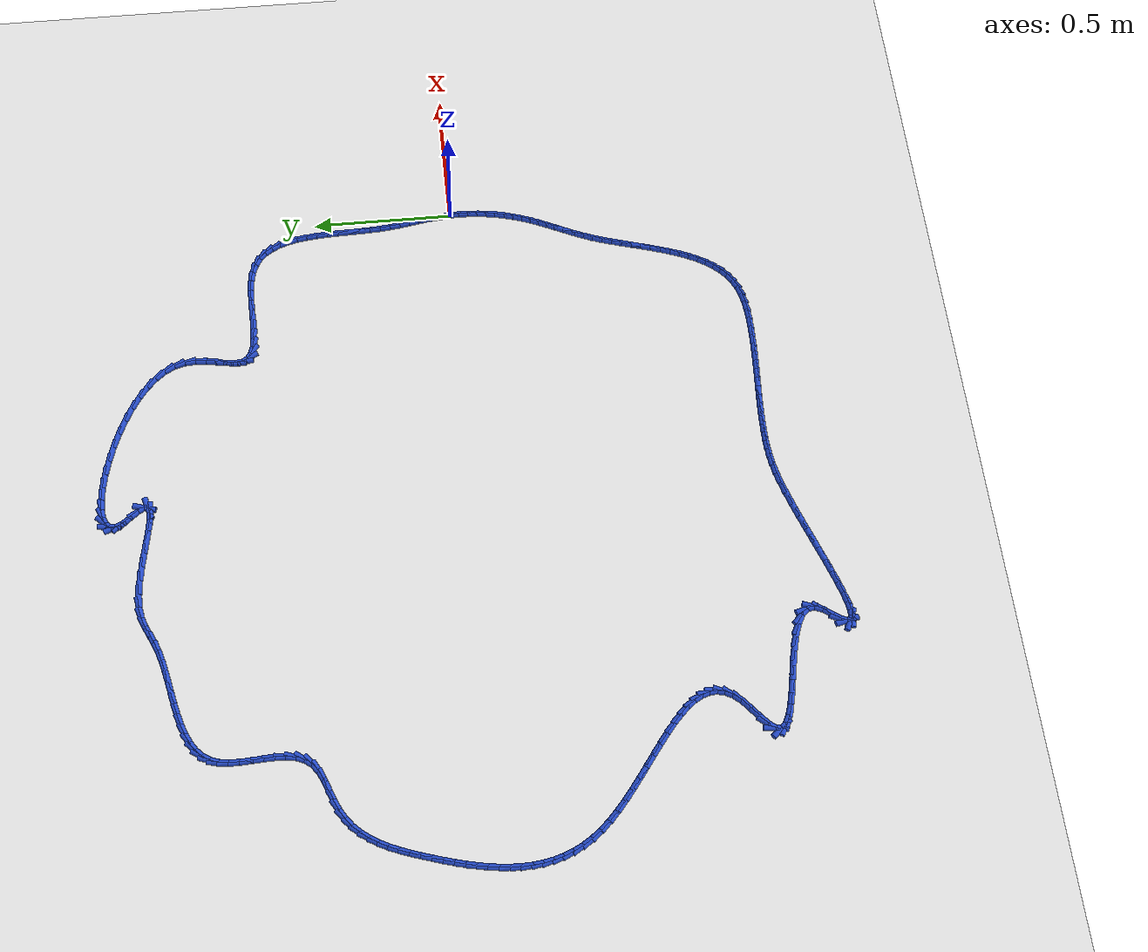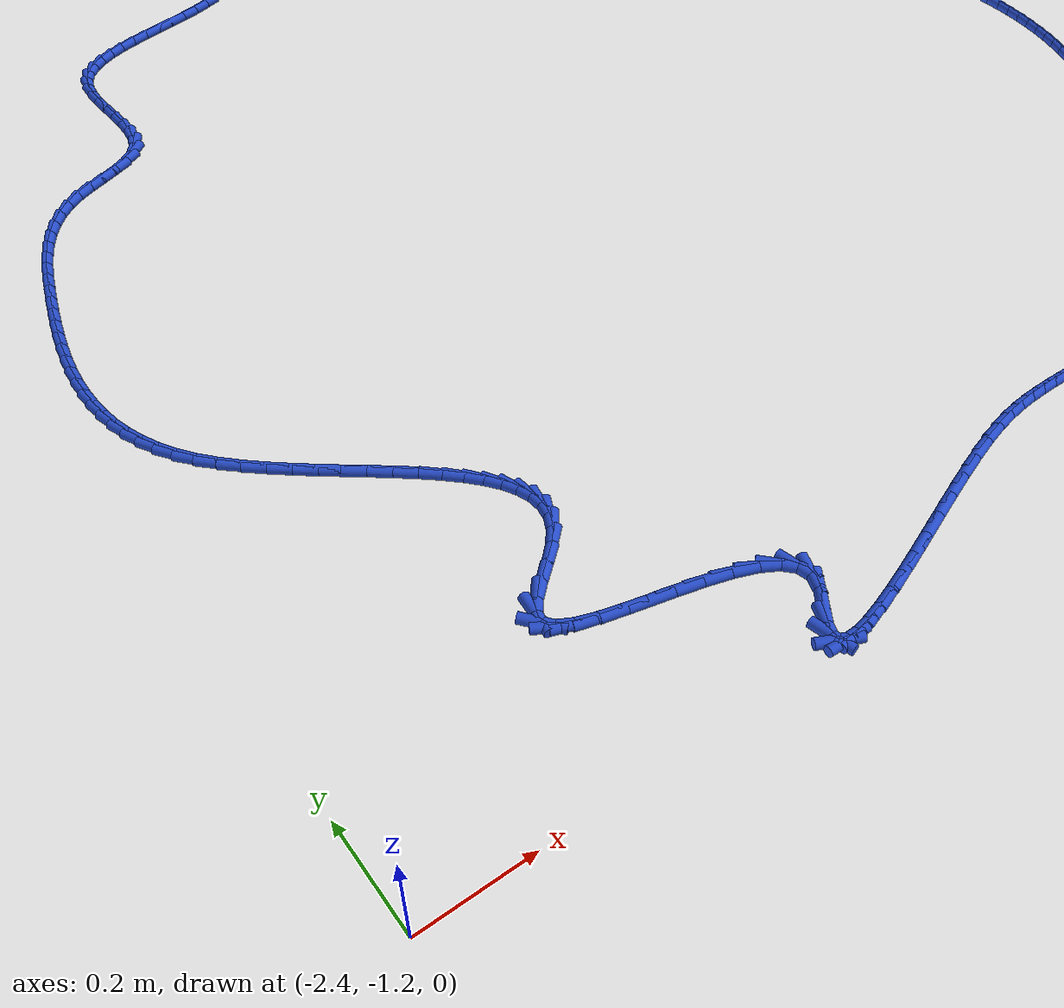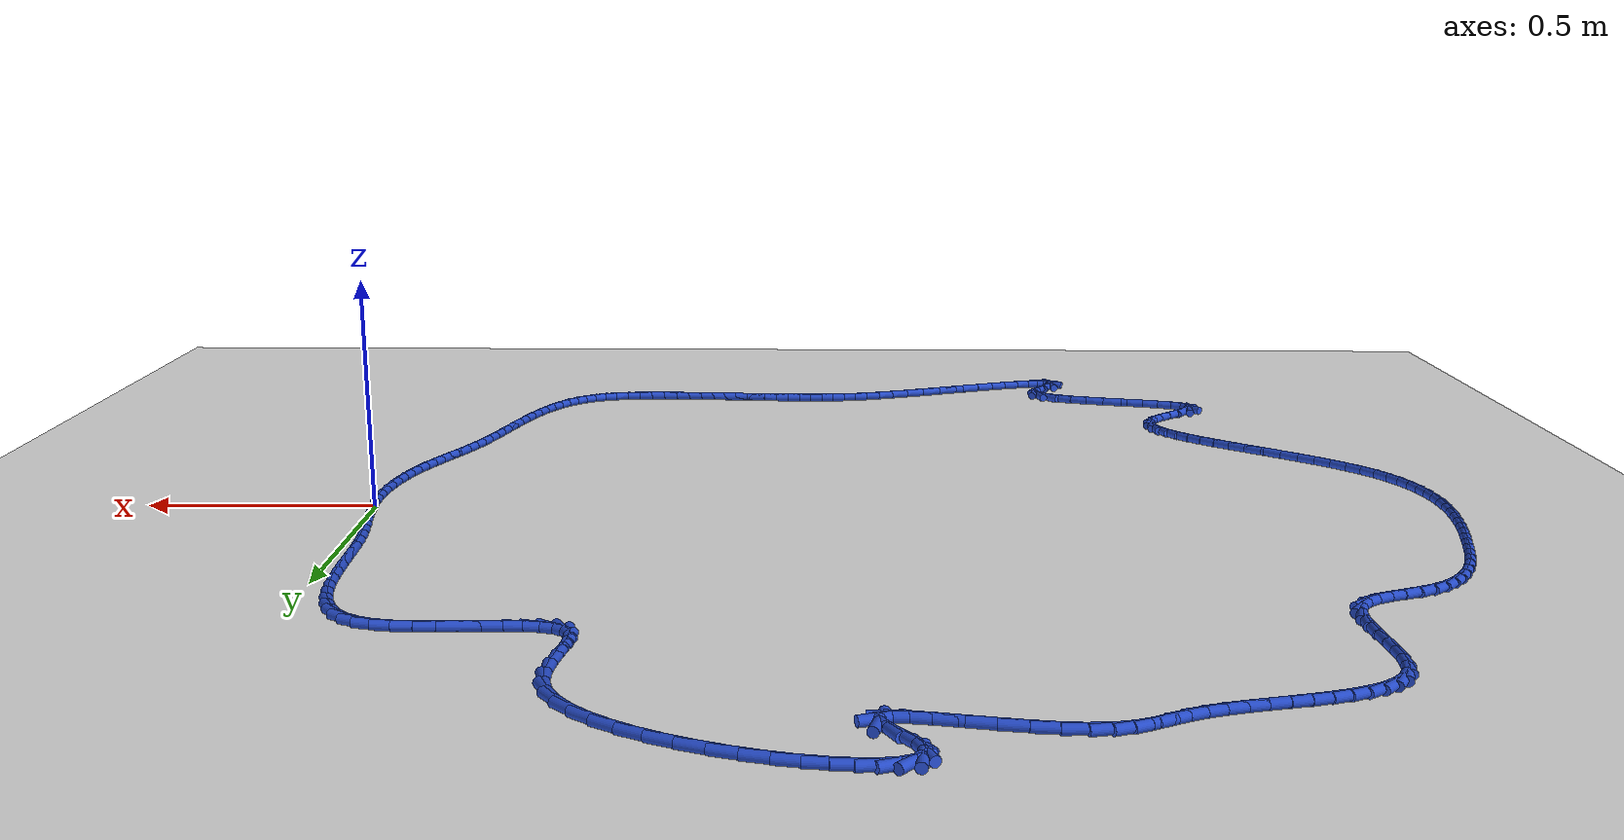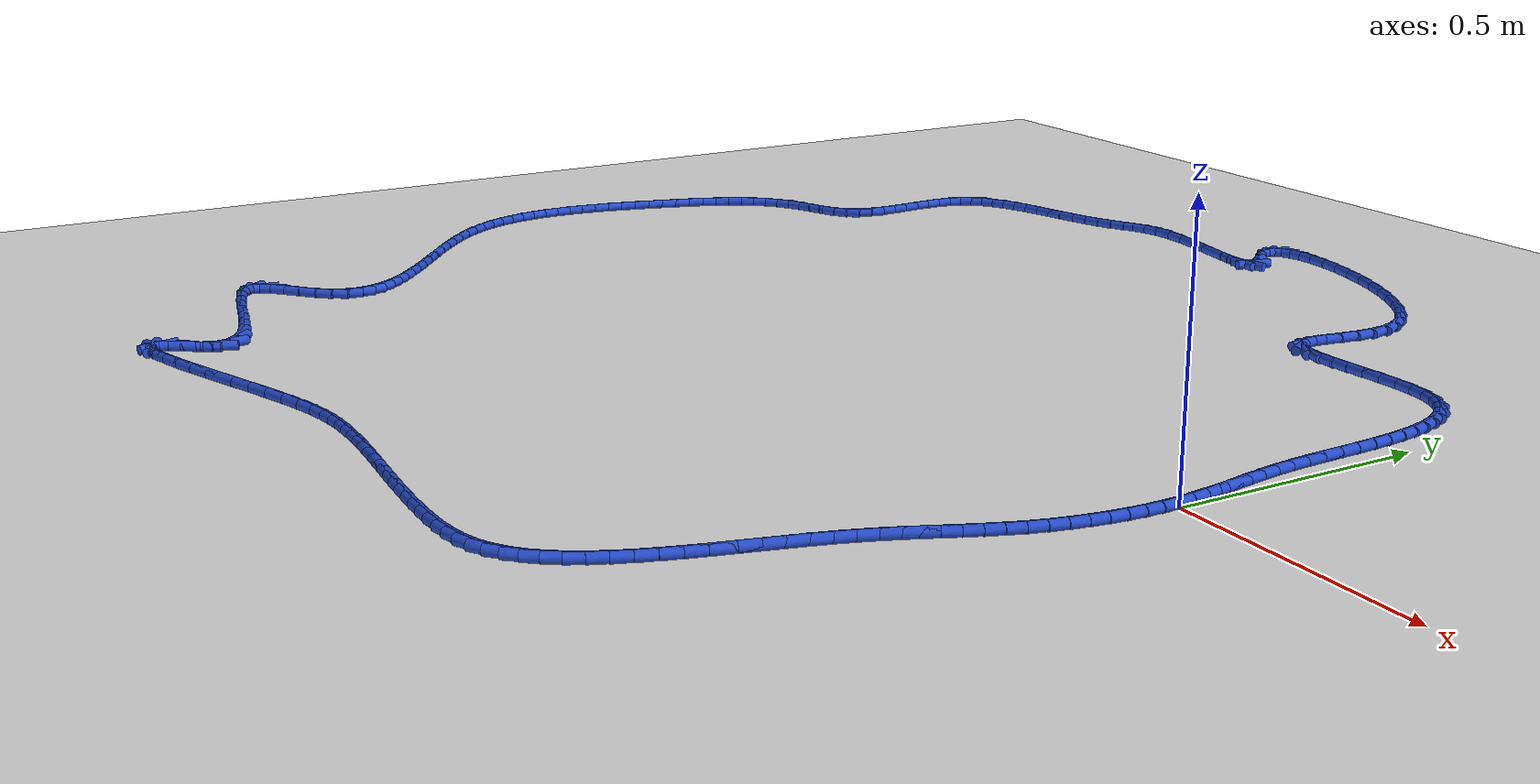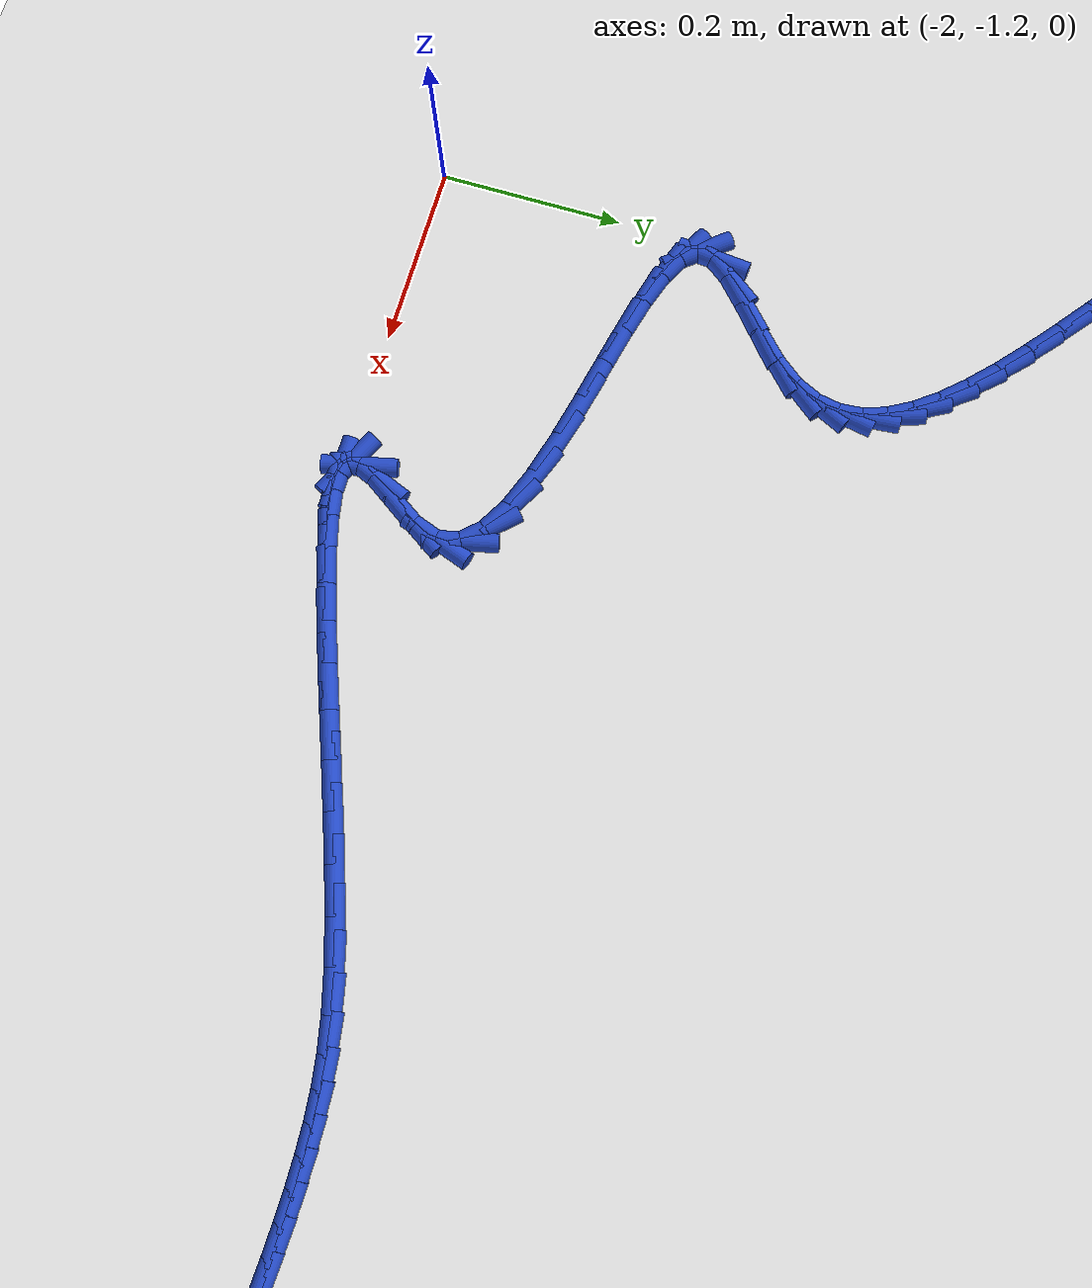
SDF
<sdf version="1.6">
 <world name="default">
  <light name="sun" type="directional">
   <pose>0 0 10 0 -0 0</pose>
   <diffuse>0.8 0.8 0.8 1</diffuse>
   <specular>0.2 0.2 0.2 1</specular>
   <attenuation>
    <range>1000</range>
    <constant>0.9</constant>
    <linear>0.01</linear>
    <quadratic>0.001</quadratic>
   </attenuation>
   <direction>-0.5 0.1 -0.9</direction>
  </light>
  <model name="ground_plane">
   <static>1</static>
   <link name="link">
    <collision name="collision">
     <geometry><plane><normal>0 0 1</normal><size>100 100</size></plane></geometry>
     <surface><friction><ode><mu>100</mu><mu2>50</mu2></ode></friction></surface>
    </collision>
    <visual name="visual">
     <cast_shadows>0</cast_shadows>
     <geometry><plane><normal>0 0 1</normal><size>100 100</size></plane></geometry>
     <material>
      <script><uri>file://media/materials/scripts/gazebo.material</uri><name>Gazebo/WhiteGlow</name></script>
     </material>
    </visual>
   </link>
  </model>
  <gravity>0 0 -9.8</gravity>
  <magnetic_field>6e-06 2.3e-05 -4.2e-05</magnetic_field>
  <atmosphere type="adiabatic"/>
  <physics name="default_physics" default="0" type="ode">
   <max_step_size>0.001</max_step_size>
   <real_time_factor>1</real_time_factor>
   <real_time_update_rate>1000</real_time_update_rate>
  </physics>
  <scene><ambient>0.4 0.4 0.4 1</ambient><background>0.7 0.7 0.7 1</background><shadows>1</shadows></scene>
  <spherical_coordinates>
   <surface_model>EARTH_WGS84</surface_model>
   <latitude_deg>0</latitude_deg>
   <longitude_deg>0</longitude_deg>
   <elevation>0</elevation>
   <heading_deg>0</heading_deg>
  </spherical_coordinates>
  <model name="line">
   <link name="link_0">
    <pose>3.122502256758253e-17 0.0 0.01 0 1.57 -1.4923464075122743</pose>
    <collision name="collision">
     <geometry><cylinder><radius>0.01</radius><length>0.08</length></cylinder></geometry>
    </collision>
    <visual name="visual">
     <material>
      <script><name>Gazebo/Blue</name><uri>file://media/materials/scripts/gazebo.material</uri></script>
     </material>
     <geometry><cylinder><radius>0.01</radius><length>0.08</length></cylinder></geometry>
    </visual>
   </link>
   <link name="link_1">
    <pose>-0.0025242396400565912 0.03211041072144942 0.01 0 1.57 -1.4527249060750735</pose>
    <collision name="collision">
     <geometry><cylinder><radius>0.01</radius><length>0.08</length></cylinder></geometry>
    </collision>
    <visual name="visual">
     <material>
      <script><name>Gazebo/Blue</name><uri>file://media/materials/scripts/gazebo.material</uri></script>
     </material>
     <geometry><cylinder><radius>0.01</radius><length>0.08</length></cylinder></geometry>
    </visual>
   </link>
   <link name="link_2">
    <pose>-0.006291301379598806 0.06386695320340485 0.01 0 1.57 -1.425345209518804</pose>
    <collision name="collision">
     <geometry><cylinder><radius>0.01</radius><length>0.08</length></cylinder></geometry>
    </collision>
    <visual name="visual">
     <material>
      <script><name>Gazebo/Blue</name><uri>file://media/materials/scripts/gazebo.material</uri></script>
     </material>
     <geometry><cylinder><radius>0.01</radius><length>0.08</length></cylinder></geometry>
    </visual>
   </link>
   <link name="link_3">
    <pose>-0.010934447581198268 0.09556390062866021 0.01 0 1.57 -1.4108151127169857</pose>
    <collision name="collision">
     <geometry><cylinder><radius>0.01</radius><length>0.08</length></cylinder></geometry>
    </collision>
    <visual name="visual">
     <material>
      <script><name>Gazebo/Blue</name><uri>file://media/materials/scripts/gazebo.material</uri></script>
     </material>
     <geometry><cylinder><radius>0.01</radius><length>0.08</length></cylinder></geometry>
    </visual>
   </link>
   <link name="link_4">
    <pose>-0.016086940607426627 0.12749552618000934 0.01 0 1.57 -1.4090964437358047</pose>
    <collision name="collision">
     <geometry><cylinder><radius>0.01</radius><length>0.08</length></cylinder></geometry>
    </collision>
    <visual name="visual">
     <material>
      <script><name>Gazebo/Blue</name><uri>file://media/materials/scripts/gazebo.material</uri></script>
     </material>
     <geometry><cylinder><radius>0.01</radius><length>0.08</length></cylinder></geometry>
    </visual>
   </link>
   <link name="link_5">
    <pose>-0.021382042820855526 0.15995610304024607 0.01 0 1.57 -1.419603406813865</pose>
    <collision name="collision">
     <geometry><cylinder><radius>0.01</radius><length>0.08</length></cylinder></geometry>
    </collision>
    <visual name="visual">
     <material>
      <script><name>Gazebo/Blue</name><uri>file://media/materials/scripts/gazebo.material</uri></script>
     </material>
     <geometry><cylinder><radius>0.01</radius><length>0.08</length></cylinder></geometry>
    </visual>
   </link>
   <link name="link_6">
    <pose>-0.026453016584056632 0.19323990439216446 0.01 0 1.57 -1.4412943942337055</pose>
    <collision name="collision">
     <geometry><cylinder><radius>0.01</radius><length>0.08</length></cylinder></geometry>
    </collision>
    <visual name="visual">
     <material>
      <script><name>Gazebo/Blue</name><uri>file://media/materials/scripts/gazebo.material</uri></script>
     </material>
     <geometry><cylinder><radius>0.01</radius><length>0.08</length></cylinder></geometry>
    </visual>
   </link>
   <link name="link_7">
    <pose>-0.030933124259601576 0.22764120341855817 0.01 0 1.57 -1.4727454228640458</pose>
    <collision name="collision">
     <geometry><cylinder><radius>0.01</radius><length>0.08</length></cylinder></geometry>
    </collision>
    <visual name="visual">
     <material>
      <script><name>Gazebo/Blue</name><uri>file://media/materials/scripts/gazebo.material</uri></script>
     </material>
     <geometry><cylinder><radius>0.01</radius><length>0.08</length></cylinder></geometry>
    </visual>
   </link>
   <link name="link_8">
    <pose>-0.0344558992944999 0.2634540144774848 0.01 0 1.57 -1.5069412213120024</pose>
    <collision name="collision">
     <geometry><cylinder><radius>0.01</radius><length>0.08</length></cylinder></geometry>
    </collision>
    <visual name="visual">
     <material>
      <script><name>Gazebo/Blue</name><uri>file://media/materials/scripts/gazebo.material</uri></script>
     </material>
     <geometry><cylinder><radius>0.01</radius><length>0.08</length></cylinder></geometry>
    </visual>
   </link>
   <link name="link_9">
    <pose>-0.03684338935002123 0.30079236320398184 0.01 0 1.57 -1.5294482146225858</pose>
    <collision name="collision">
     <geometry><cylinder><radius>0.01</radius><length>0.08</length></cylinder></geometry>
    </collision>
    <visual name="visual">
     <material>
      <script><name>Gazebo/Blue</name><uri>file://media/materials/scripts/gazebo.material</uri></script>
     </material>
     <geometry><cylinder><radius>0.01</radius><length>0.08</length></cylinder></geometry>
    </visual>
   </link>
   <link name="link_10">
    <pose>-0.03843551519082392 0.33927582276470847 0.01 0 1.57 -1.539532102239141</pose>
    <collision name="collision">
     <geometry><cylinder><radius>0.01</radius><length>0.08</length></cylinder></geometry>
    </collision>
    <visual name="visual">
     <material>
      <script><name>Gazebo/Blue</name><uri>file://media/materials/scripts/gazebo.material</uri></script>
     </material>
     <geometry><cylinder><radius>0.01</radius><length>0.08</length></cylinder></geometry>
    </visual>
   </link>
   <link name="link_11">
    <pose>-0.03966034580949153 0.3784398045720334 0.01 0 1.57 -1.5381617224673751</pose>
    <collision name="collision">
     <geometry><cylinder><radius>0.01</radius><length>0.08</length></cylinder></geometry>
    </collision>
    <visual name="visual">
     <material>
      <script><name>Gazebo/Blue</name><uri>file://media/materials/scripts/gazebo.material</uri></script>
     </material>
     <geometry><cylinder><radius>0.01</radius><length>0.08</length></cylinder></geometry>
    </visual>
   </link>
   <link name="link_12">
    <pose>-0.04094595019860771 0.4178197200383258 0.01 0 1.57 -1.525481343751991</pose>
    <collision name="collision">
     <geometry><cylinder><radius>0.01</radius><length>0.08</length></cylinder></geometry>
    </collision>
    <visual name="visual">
     <material>
      <script><name>Gazebo/Blue</name><uri>file://media/materials/scripts/gazebo.material</uri></script>
     </material>
     <geometry><cylinder><radius>0.01</radius><length>0.08</length></cylinder></geometry>
    </visual>
   </link>
   <link name="link_13">
    <pose>-0.04272039735075603 0.4569509805759544 0.01 0 1.57 -1.5008559892053672</pose>
    <collision name="collision">
     <geometry><cylinder><radius>0.01</radius><length>0.08</length></cylinder></geometry>
    </collision>
    <visual name="visual">
     <material>
      <script><name>Gazebo/Blue</name><uri>file://media/materials/scripts/gazebo.material</uri></script>
     </material>
     <geometry><cylinder><radius>0.01</radius><length>0.08</length></cylinder></geometry>
    </visual>
   </link>
   <link name="link_14">
    <pose>-0.04541175625852012 0.49536899759728836 0.01 0 1.57 -1.4628311197172172</pose>
    <collision name="collision">
     <geometry><cylinder><radius>0.01</radius><length>0.08</length></cylinder></geometry>
    </collision>
    <visual name="visual">
     <material>
      <script><name>Gazebo/Blue</name><uri>file://media/materials/scripts/gazebo.material</uri></script>
     </material>
     <geometry><cylinder><radius>0.01</radius><length>0.08</length></cylinder></geometry>
    </visual>
   </link>
   <link name="link_15">
    <pose>-0.0494480959144836 0.5326091825146966 0.01 0 1.57 -1.4090270414760842</pose>
    <collision name="collision">
     <geometry><cylinder><radius>0.01</radius><length>0.08</length></cylinder></geometry>
    </collision>
    <visual name="visual">
     <material>
      <script><name>Gazebo/Blue</name><uri>file://media/materials/scripts/gazebo.material</uri></script>
     </material>
     <geometry><cylinder><radius>0.01</radius><length>0.08</length></cylinder></geometry>
    </visual>
   </link>
   <link name="link_16">
    <pose>-0.05525748531123002 0.5682069467405477 0.01 0 1.57 -1.336021482420716</pose>
    <collision name="collision">
     <geometry><cylinder><radius>0.01</radius><length>0.08</length></cylinder></geometry>
    </collision>
    <visual name="visual">
     <material>
      <script><name>Gazebo/Blue</name><uri>file://media/materials/scripts/gazebo.material</uri></script>
     </material>
     <geometry><cylinder><radius>0.01</radius><length>0.08</length></cylinder></geometry>
    </visual>
   </link>
   <link name="link_17">
    <pose>-0.06326799344134307 0.6016977016872112 0.01 0 1.57 -1.2393753012844513</pose>
    <collision name="collision">
     <geometry><cylinder><radius>0.01</radius><length>0.08</length></cylinder></geometry>
    </collision>
    <visual name="visual">
     <material>
      <script><name>Gazebo/Blue</name><uri>file://media/materials/scripts/gazebo.material</uri></script>
     </material>
     <geometry><cylinder><radius>0.01</radius><length>0.08</length></cylinder></geometry>
    </visual>
   </link>
   <link name="link_18">
    <pose>-0.07390768929740628 0.6326168587670558 0.01 0 1.57 -1.1141892738138877</pose>
    <collision name="collision">
     <geometry><cylinder><radius>0.01</radius><length>0.08</length></cylinder></geometry>
    </collision>
    <visual name="visual">
     <material>
      <script><name>Gazebo/Blue</name><uri>file://media/materials/scripts/gazebo.material</uri></script>
     </material>
     <geometry><cylinder><radius>0.01</radius><length>0.08</length></cylinder></geometry>
    </visual>
   </link>
   <link name="link_19">
    <pose>-0.08760464187200327 0.6604998293924501 0.01 0 1.57 -0.956918984813352</pose>
    <collision name="collision">
     <geometry><cylinder><radius>0.01</radius><length>0.08</length></cylinder></geometry>
    </collision>
    <visual name="visual">
     <material>
      <script><name>Gazebo/Blue</name><uri>file://media/materials/scripts/gazebo.material</uri></script>
     </material>
     <geometry><cylinder><radius>0.01</radius><length>0.08</length></cylinder></geometry>
    </visual>
   </link>
   <link name="link_20">
    <pose>-0.10478692015771768 0.6848820249757636 0.01 0 1.57 -0.7690469329252106</pose>
    <collision name="collision">
     <geometry><cylinder><radius>0.01</radius><length>0.08</length></cylinder></geometry>
    </collision>
    <visual name="visual">
     <material>
      <script><name>Gazebo/Blue</name><uri>file://media/materials/scripts/gazebo.material</uri></script>
     </material>
     <geometry><cylinder><radius>0.01</radius><length>0.08</length></cylinder></geometry>
    </visual>
   </link>
   <link name="link_21">
    <pose>-0.1258825931471331 0.7052988569293648 0.01 0 1.57 -0.5611020470445771</pose>
    <collision name="collision">
     <geometry><cylinder><radius>0.01</radius><length>0.08</length></cylinder></geometry>
    </collision>
    <visual name="visual">
     <material>
      <script><name>Gazebo/Blue</name><uri>file://media/materials/scripts/gazebo.material</uri></script>
     </material>
     <geometry><cylinder><radius>0.01</radius><length>0.08</length></cylinder></geometry>
    </visual>
   </link>
   <link name="link_22">
    <pose>-0.15131972983283312 0.721285736665623 0.01 0 1.57 -0.35248358245858363</pose>
    <collision name="collision">
     <geometry><cylinder><radius>0.01</radius><length>0.08</length></cylinder></geometry>
    </collision>
    <visual name="visual">
     <material>
      <script><name>Gazebo/Blue</name><uri>file://media/materials/scripts/gazebo.material</uri></script>
     </material>
     <geometry><cylinder><radius>0.01</radius><length>0.08</length></cylinder></geometry>
    </visual>
   </link>
   <link name="link_23">
    <pose>-0.18151154100221772 0.7323916604707373 0.01 0 1.57 -0.18228051396166303</pose>
    <collision name="collision">
     <geometry><cylinder><radius>0.01</radius><length>0.08</length></cylinder></geometry>
    </collision>
    <visual name="visual">
     <material>
      <script><name>Gazebo/Blue</name><uri>file://media/materials/scripts/gazebo.material</uri></script>
     </material>
     <geometry><cylinder><radius>0.01</radius><length>0.08</length></cylinder></geometry>
    </visual>
   </link>
   <link name="link_24">
    <pose>-0.21619424163523424 0.7387846026645604 0.01 0 1.57 -0.07122660608630609</pose>
    <collision name="collision">
     <geometry><cylinder><radius>0.01</radius><length>0.08</length></cylinder></geometry>
    </collision>
    <visual name="visual">
     <material>
      <script><name>Gazebo/Blue</name><uri>file://media/materials/scripts/gazebo.material</uri></script>
     </material>
     <geometry><cylinder><radius>0.01</radius><length>0.08</length></cylinder></geometry>
    </visual>
   </link>
   <link name="link_25">
    <pose>-0.2541623573352507 0.7414935252306911 0.01 0 1.57 -0.002939330916850914</pose>
    <collision name="collision">
     <geometry><cylinder><radius>0.01</radius><length>0.08</length></cylinder></geometry>
    </collision>
    <visual name="visual">
     <material>
      <script><name>Gazebo/Blue</name><uri>file://media/materials/scripts/gazebo.material</uri></script>
     </material>
     <geometry><cylinder><radius>0.01</radius><length>0.08</length></cylinder></geometry>
    </visual>
   </link>
   <link name="link_26">
    <pose>-0.2941408028356902 0.7416110354499748 0.01 0 1.57 0.033914028286608056</pose>
    <collision name="collision">
     <geometry><cylinder><radius>0.01</radius><length>0.08</length></cylinder></geometry>
    </collision>
    <visual name="visual">
     <material>
      <script><name>Gazebo/Blue</name><uri>file://media/materials/scripts/gazebo.material</uri></script>
     </material>
     <geometry><cylinder><radius>0.01</radius><length>0.08</length></cylinder></geometry>
    </visual>
   </link>
   <link name="link_27">
    <pose>-0.3348544928699761 0.740229740603257 0.01 0 1.57 0.04446460793757391</pose>
    <collision name="collision">
     <geometry><cylinder><radius>0.01</radius><length>0.08</length></cylinder></geometry>
    </collision>
    <visual name="visual">
     <material>
      <script><name>Gazebo/Blue</name><uri>file://media/materials/scripts/gazebo.material</uri></script>
     </material>
     <geometry><cylinder><radius>0.01</radius><length>0.08</length></cylinder></geometry>
    </visual>
   </link>
   <link name="link_28">
    <pose>-0.37502834217153114 0.7384422479713829 0.01 0 1.57 0.02869686565206392</pose>
    <collision name="collision">
     <geometry><cylinder><radius>0.01</radius><length>0.08</length></cylinder></geometry>
    </collision>
    <visual name="visual">
     <material>
      <script><name>Gazebo/Blue</name><uri>file://media/materials/scripts/gazebo.material</uri></script>
     </material>
     <geometry><cylinder><radius>0.01</radius><length>0.08</length></cylinder></geometry>
    </visual>
   </link>
   <link name="link_29">
    <pose>-0.4133872654737788 0.7373411648351982 0.01 0 1.57 -0.019219480430270774</pose>
    <collision name="collision">
     <geometry><cylinder><radius>0.01</radius><length>0.08</length></cylinder></geometry>
    </collision>
    <visual name="visual">
     <material>
      <script><name>Gazebo/Blue</name><uri>file://media/materials/scripts/gazebo.material</uri></script>
     </material>
     <geometry><cylinder><radius>0.01</radius><length>0.08</length></cylinder></geometry>
    </visual>
   </link>
   <link name="link_30">
    <pose>-0.4486561775101417 0.7380190984755476 0.01 0 1.57 -0.11435710970234506</pose>
    <collision name="collision">
     <geometry><cylinder><radius>0.01</radius><length>0.08</length></cylinder></geometry>
    </collision>
    <visual name="visual">
     <material>
      <script><name>Gazebo/Blue</name><uri>file://media/materials/scripts/gazebo.material</uri></script>
     </material>
     <geometry><cylinder><radius>0.01</radius><length>0.08</length></cylinder></geometry>
    </visual>
   </link>
   <link name="link_31">
    <pose>-0.4795599930140432 0.7415686561732768 0.01 0 1.57 -0.28908374782690727</pose>
    <collision name="collision">
     <geometry><cylinder><radius>0.01</radius><length>0.08</length></cylinder></geometry>
    </collision>
    <visual name="visual">
     <material>
      <script><name>Gazebo/Blue</name><uri>file://media/materials/scripts/gazebo.material</uri></script>
     </material>
     <geometry><cylinder><radius>0.01</radius><length>0.08</length></cylinder></geometry>
    </visual>
   </link>
   <link name="link_32">
    <pose>-0.5048236267189065 0.7490824452092313 0.01 0 1.57 -0.600661807914167</pose>
    <collision name="collision">
     <geometry><cylinder><radius>0.01</radius><length>0.08</length></cylinder></geometry>
    </collision>
    <visual name="visual">
     <material>
      <script><name>Gazebo/Blue</name><uri>file://media/materials/scripts/gazebo.material</uri></script>
     </material>
     <geometry><cylinder><radius>0.01</radius><length>0.08</length></cylinder></geometry>
    </visual>
   </link>
   <link name="link_33">
    <pose>-0.5231719933581545 0.7616530728642563 0.01 0 1.57 -1.0708802898240515</pose>
    <collision name="collision">
     <geometry><cylinder><radius>0.01</radius><length>0.08</length></cylinder></geometry>
    </collision>
    <visual name="visual">
     <material>
      <script><name>Gazebo/Blue</name><uri>file://media/materials/scripts/gazebo.material</uri></script>
     </material>
     <geometry><cylinder><radius>0.01</radius><length>0.08</length></cylinder></geometry>
    </visual>
   </link>
   <link name="link_34">
    <pose>-0.5333804208115077 0.7803432036538778 0.01 0 1.57 -1.4700803531865658</pose>
    <collision name="collision">
     <geometry><cylinder><radius>0.01</radius><length>0.08</length></cylinder></geometry>
    </collision>
    <visual name="visual">
     <material>
      <script><name>Gazebo/Blue</name><uri>file://media/materials/scripts/gazebo.material</uri></script>
     </material>
     <geometry><cylinder><radius>0.01</radius><length>0.08</length></cylinder></geometry>
    </visual>
   </link>
   <link name="link_35">
    <pose>-0.5358947516386539 0.8052233039727204 0.01 0 1.57 1.4802786324896795</pose>
    <collision name="collision">
     <geometry><cylinder><radius>0.01</radius><length>0.08</length></cylinder></geometry>
    </collision>
    <visual name="visual">
     <material>
      <script><name>Gazebo/Blue</name><uri>file://media/materials/scripts/gazebo.material</uri></script>
     </material>
     <geometry><cylinder><radius>0.01</radius><length>0.08</length></cylinder></geometry>
    </visual>
   </link>
   <link name="link_36">
    <pose>-0.5331769474389734 0.8351663712277464 0.01 0 1.57 1.413339230249264</pose>
    <collision name="collision">
     <geometry><cylinder><radius>0.01</radius><length>0.08</length></cylinder></geometry>
    </collision>
    <visual name="visual">
     <material>
      <script><name>Gazebo/Blue</name><uri>file://media/materials/scripts/gazebo.material</uri></script>
     </material>
     <geometry><cylinder><radius>0.01</radius><length>0.08</length></cylinder></geometry>
    </visual>
   </link>
   <link name="link_37">
    <pose>-0.5278092709081046 0.8689739502831298 0.01 0 1.57 1.4228653549968964</pose>
    <collision name="collision">
     <geometry><cylinder><radius>0.01</radius><length>0.08</length></cylinder></geometry>
    </collision>
    <visual name="visual">
     <material>
      <script><name>Gazebo/Blue</name><uri>file://media/materials/scripts/gazebo.material</uri></script>
     </material>
     <geometry><cylinder><radius>0.01</radius><length>0.08</length></cylinder></geometry>
    </visual>
   </link>
   <link name="link_38">
    <pose>-0.5223739847416864 0.9054475860030436 0.01 0 1.57 1.493970031074479</pose>
    <collision name="collision">
     <geometry><cylinder><radius>0.01</radius><length>0.08</length></cylinder></geometry>
    </collision>
    <visual name="visual">
     <material>
      <script><name>Gazebo/Blue</name><uri>file://media/materials/scripts/gazebo.material</uri></script>
     </material>
     <geometry><cylinder><radius>0.01</radius><length>0.08</length></cylinder></geometry>
    </visual>
   </link>
   <link name="link_39">
    <pose>-0.5194533516353569 0.9433888232516626 0.01 0 1.57 -1.513902524757434</pose>
    <collision name="collision">
     <geometry><cylinder><radius>0.01</radius><length>0.08</length></cylinder></geometry>
    </collision>
    <visual name="visual">
     <material>
      <script><name>Gazebo/Blue</name><uri>file://media/materials/scripts/gazebo.material</uri></script>
     </material>
     <geometry><cylinder><radius>0.01</radius><length>0.08</length></cylinder></geometry>
    </visual>
   </link>
   <link name="link_40">
    <pose>-0.5216296342847545 0.9815992068931589 0.01 0 1.57 -1.312798483066644</pose>
    <collision name="collision">
     <geometry><cylinder><radius>0.01</radius><length>0.08</length></cylinder></geometry>
    </collision>
    <visual name="visual">
     <material>
      <script><name>Gazebo/Blue</name><uri>file://media/materials/scripts/gazebo.material</uri></script>
     </material>
     <geometry><cylinder><radius>0.01</radius><length>0.08</length></cylinder></geometry>
    </visual>
   </link>
   <link name="link_41">
    <pose>-0.5314684991429615 1.0188847467095898 0.01 0 1.57 -1.0849188378656638</pose>
    <collision name="collision">
     <geometry><cylinder><radius>0.01</radius><length>0.08</length></cylinder></geometry>
    </collision>
    <visual name="visual">
     <material>
      <script><name>Gazebo/Blue</name><uri>file://media/materials/scripts/gazebo.material</uri></script>
     </material>
     <geometry><cylinder><radius>0.01</radius><length>0.08</length></cylinder></geometry>
    </visual>
   </link>
   <link name="link_42">
    <pose>-0.5502262236348582 1.054403719839127 0.01 0 1.57 -0.8980681484589687</pose>
    <collision name="collision">
     <geometry><cylinder><radius>0.01</radius><length>0.08</length></cylinder></geometry>
    </collision>
    <visual name="visual">
     <material>
      <script><name>Gazebo/Blue</name><uri>file://media/materials/scripts/gazebo.material</uri></script>
     </material>
     <geometry><cylinder><radius>0.01</radius><length>0.08</length></cylinder></geometry>
    </visual>
   </link>
   <link name="link_43">
    <pose>-0.5769251320058825 1.0879154079825784 0.01 0 1.57 -0.7526490560378257</pose>
    <collision name="collision">
     <geometry><cylinder><radius>0.01</radius><length>0.08</length></cylinder></geometry>
    </collision>
    <visual name="visual">
     <material>
      <script><name>Gazebo/Blue</name><uri>file://media/materials/scripts/gazebo.material</uri></script>
     </material>
     <geometry><cylinder><radius>0.01</radius><length>0.08</length></cylinder></geometry>
    </visual>
   </link>
   <link name="link_44">
    <pose>-0.6103693309822446 1.1192378003042316 0.01 0 1.57 -0.6386563676755015</pose>
    <collision name="collision">
     <geometry><cylinder><radius>0.01</radius><length>0.08</length></cylinder></geometry>
    </collision>
    <visual name="visual">
     <material>
      <script><name>Gazebo/Blue</name><uri>file://media/materials/scripts/gazebo.material</uri></script>
     </material>
     <geometry><cylinder><radius>0.01</radius><length>0.08</length></cylinder></geometry>
    </visual>
   </link>
   <link name="link_45">
    <pose>-0.6493629272901551 1.148188885968375 0.01 0 1.57 -0.5470005143522644</pose>
    <collision name="collision">
     <geometry><cylinder><radius>0.01</radius><length>0.08</length></cylinder></geometry>
    </collision>
    <visual name="visual">
     <material>
      <script><name>Gazebo/Blue</name><uri>file://media/materials/scripts/gazebo.material</uri></script>
     </material>
     <geometry><cylinder><radius>0.01</radius><length>0.08</length></cylinder></geometry>
    </visual>
   </link>
   <link name="link_46">
    <pose>-0.6927100276558247 1.1745866541392977 0.01 0 1.57 -0.4706771961666823</pose>
    <collision name="collision">
     <geometry><cylinder><radius>0.01</radius><length>0.08</length></cylinder></geometry>
    </collision>
    <visual name="visual">
     <material>
      <script><name>Gazebo/Blue</name><uri>file://media/materials/scripts/gazebo.material</uri></script>
     </material>
     <geometry><cylinder><radius>0.01</radius><length>0.08</length></cylinder></geometry>
    </visual>
   </link>
   <link name="link_47">
    <pose>-0.7392147388054642 1.1982490939812878 0.01 0 1.57 -0.4044345482107053</pose>
    <collision name="collision">
     <geometry><cylinder><radius>0.01</radius><length>0.08</length></cylinder></geometry>
    </collision>
    <visual name="visual">
     <material>
      <script><name>Gazebo/Blue</name><uri>file://media/materials/scripts/gazebo.material</uri></script>
     </material>
     <geometry><cylinder><radius>0.01</radius><length>0.08</length></cylinder></geometry>
    </visual>
   </link>
   <link name="link_48">
    <pose>-0.7876811674652838 1.2189941946586333 0.01 0 1.57 -0.344154830333732</pose>
    <collision name="collision">
     <geometry><cylinder><radius>0.01</radius><length>0.08</length></cylinder></geometry>
    </collision>
    <visual name="visual">
     <material>
      <script><name>Gazebo/Blue</name><uri>file://media/materials/scripts/gazebo.material</uri></script>
     </material>
     <geometry><cylinder><radius>0.01</radius><length>0.08</length></cylinder></geometry>
    </visual>
   </link>
   <link name="link_49">
    <pose>-0.8369134203614942 1.2366399453356236 0.01 0 1.57 -0.28625523133374653</pose>
    <collision name="collision">
     <geometry><cylinder><radius>0.01</radius><length>0.08</length></cylinder></geometry>
    </collision>
    <visual name="visual">
     <material>
      <script><name>Gazebo/Blue</name><uri>file://media/materials/scripts/gazebo.material</uri></script>
     </material>
     <geometry><cylinder><radius>0.01</radius><length>0.08</length></cylinder></geometry>
    </visual>
   </link>
   <link name="link_50">
    <pose>-0.8857156042203059 1.251004335176546 0.01 0 1.57 -0.22708456521171863</pose>
    <collision name="collision">
     <geometry><cylinder><radius>0.01</radius><length>0.08</length></cylinder></geometry>
    </collision>
    <visual name="visual">
     <material>
      <script><name>Gazebo/Blue</name><uri>file://media/materials/scripts/gazebo.material</uri></script>
     </material>
     <geometry><cylinder><radius>0.01</radius><length>0.08</length></cylinder></geometry>
    </visual>
   </link>
   <link name="link_51">
    <pose>-0.9328918257679296 1.26190535334569 0.01 0 1.57 -0.1621471995024719</pose>
    <collision name="collision">
     <geometry><cylinder><radius>0.01</radius><length>0.08</length></cylinder></geometry>
    </collision>
    <visual name="visual">
     <material>
      <script><name>Gazebo/Blue</name><uri>file://media/materials/scripts/gazebo.material</uri></script>
     </material>
     <geometry><cylinder><radius>0.01</radius><length>0.08</length></cylinder></geometry>
    </visual>
   </link>
   <link name="link_52">
    <pose>-0.9772461917305759 1.2691609890073432 0.01 0 1.57 -0.08478706417523625</pose>
    <collision name="collision">
     <geometry><cylinder><radius>0.01</radius><length>0.08</length></cylinder></geometry>
    </collision>
    <visual name="visual">
     <material>
      <script><name>Gazebo/Blue</name><uri>file://media/materials/scripts/gazebo.material</uri></script>
     </material>
     <geometry><cylinder><radius>0.01</radius><length>0.08</length></cylinder></geometry>
    </visual>
   </link>
   <link name="link_53">
    <pose>-1.0175828088344554 1.2725892313257945 0.01 0 1.57 0.01654497751420317</pose>
    <collision name="collision">
     <geometry><cylinder><radius>0.01</radius><length>0.08</length></cylinder></geometry>
    </collision>
    <visual name="visual">
     <material>
      <script><name>Gazebo/Blue</name><uri>file://media/materials/scripts/gazebo.material</uri></script>
     </material>
     <geometry><cylinder><radius>0.01</radius><length>0.08</length></cylinder></geometry>
    </visual>
   </link>
   <link name="link_54">
    <pose>-1.0527057838057785 1.2720080694653322 0.01 0 1.57 0.16470825440545375</pose>
    <collision name="collision">
     <geometry><cylinder><radius>0.01</radius><length>0.08</length></cylinder></geometry>
    </collision>
    <visual name="visual">
     <material>
      <script><name>Gazebo/Blue</name><uri>file://media/materials/scripts/gazebo.material</uri></script>
     </material>
     <geometry><cylinder><radius>0.01</radius><length>0.08</length></cylinder></geometry>
    </visual>
   </link>
   <link name="link_55">
    <pose>-1.0814192233707556 1.2672354925902447 0.01 0 1.57 0.4088758405011477</pose>
    <collision name="collision">
     <geometry><cylinder><radius>0.01</radius><length>0.08</length></cylinder></geometry>
    </collision>
    <visual name="visual">
     <material>
      <script><name>Gazebo/Blue</name><uri>file://media/materials/scripts/gazebo.material</uri></script>
     </material>
     <geometry><cylinder><radius>0.01</radius><length>0.08</length></cylinder></geometry>
    </visual>
   </link>
   <link name="link_56">
    <pose>-1.102527234255598 1.2580894898648205 0.01 0 1.57 0.8389743264750044</pose>
    <collision name="collision">
     <geometry><cylinder><radius>0.01</radius><length>0.08</length></cylinder></geometry>
    </collision>
    <visual name="visual">
     <material>
      <script><name>Gazebo/Blue</name><uri>file://media/materials/scripts/gazebo.material</uri></script>
     </material>
     <geometry><cylinder><radius>0.01</radius><length>0.08</length></cylinder></geometry>
    </visual>
   </link>
   <link name="link_57">
    <pose>-1.1148339231865156 1.2443880504533482 0.01 0 1.57 1.4461950196633189</pose>
    <collision name="collision">
     <geometry><cylinder><radius>0.01</radius><length>0.08</length></cylinder></geometry>
    </collision>
    <visual name="visual">
     <material>
      <script><name>Gazebo/Blue</name><uri>file://media/materials/scripts/gazebo.material</uri></script>
     </material>
     <geometry><cylinder><radius>0.01</radius><length>0.08</length></cylinder></geometry>
    </visual>
   </link>
   <link name="link_58">
    <pose>-1.1171433968897193 1.2259491635201158 0.01 0 1.57 -1.20737013856195</pose>
    <collision name="collision">
     <geometry><cylinder><radius>0.01</radius><length>0.08</length></cylinder></geometry>
    </collision>
    <visual name="visual">
     <material>
      <script><name>Gazebo/Blue</name><uri>file://media/materials/scripts/gazebo.material</uri></script>
     </material>
     <geometry><cylinder><radius>0.01</radius><length>0.08</length></cylinder></geometry>
    </visual>
   </link>
   <link name="link_59">
    <pose>-1.1082597620914196 1.2025908182294125 0.01 0 1.57 -0.95328428460516</pose>
    <collision name="collision">
     <geometry><cylinder><radius>0.01</radius><length>0.08</length></cylinder></geometry>
    </collision>
    <visual name="visual">
     <material>
      <script><name>Gazebo/Blue</name><uri>file://media/materials/scripts/gazebo.material</uri></script>
     </material>
     <geometry><cylinder><radius>0.01</radius><length>0.08</length></cylinder></geometry>
    </visual>
   </link>
   <link name="link_60">
    <pose>-1.0885902472112672 1.1748935050328044 0.01 0 1.57 -0.9076793269784613</pose>
    <collision name="collision">
     <geometry><cylinder><radius>0.01</radius><length>0.08</length></cylinder></geometry>
    </collision>
    <visual name="visual">
     <material>
      <script><name>Gazebo/Blue</name><uri>file://media/materials/scripts/gazebo.material</uri></script>
     </material>
     <geometry><cylinder><radius>0.01</radius><length>0.08</length></cylinder></geometry>
    </visual>
   </link>
   <link name="link_61">
    <pose>-1.0672579071118968 1.1475832692138281 0.01 0 1.57 -1.0780925915806356</pose>
    <collision name="collision">
     <geometry><cylinder><radius>0.01</radius><length>0.08</length></cylinder></geometry>
    </collision>
    <visual name="visual">
     <material>
      <script><name>Gazebo/Blue</name><uri>file://media/materials/scripts/gazebo.material</uri></script>
     </material>
     <geometry><cylinder><radius>0.01</radius><length>0.08</length></cylinder></geometry>
    </visual>
   </link>
   <link name="link_62">
    <pose>-1.0559970106703855 1.1266080281186397 0.01 0 1.57 1.2945069952393078</pose>
    <collision name="collision">
     <geometry><cylinder><radius>0.01</radius><length>0.08</length></cylinder></geometry>
    </collision>
    <visual name="visual">
     <material>
      <script><name>Gazebo/Blue</name><uri>file://media/materials/scripts/gazebo.material</uri></script>
     </material>
     <geometry><cylinder><radius>0.01</radius><length>0.08</length></cylinder></geometry>
    </visual>
   </link>
   <link name="link_63">
    <pose>-1.0595266218368762 1.1141597050144265 0.01 0 1.57 0.3115966419591782</pose>
    <collision name="collision">
     <geometry><cylinder><radius>0.01</radius><length>0.08</length></cylinder></geometry>
    </collision>
    <visual name="visual">
     <material>
      <script><name>Gazebo/Blue</name><uri>file://media/materials/scripts/gazebo.material</uri></script>
     </material>
     <geometry><cylinder><radius>0.01</radius><length>0.08</length></cylinder></geometry>
    </visual>
   </link>
   <link name="link_64">
    <pose>-1.0759286762650775 1.108876785668117 0.01 0 1.57 -0.014079511973966095</pose>
    <collision name="collision">
     <geometry><cylinder><radius>0.01</radius><length>0.08</length></cylinder></geometry>
    </collision>
    <visual name="visual">
     <material>
      <script><name>Gazebo/Blue</name><uri>file://media/materials/scripts/gazebo.material</uri></script>
     </material>
     <geometry><cylinder><radius>0.01</radius><length>0.08</length></cylinder></geometry>
    </visual>
   </link>
   <link name="link_65">
    <pose>-1.1030246500284233 1.1092583089656232 0.01 0 1.57 -0.12694163851758683</pose>
    <collision name="collision">
     <geometry><cylinder><radius>0.01</radius><length>0.08</length></cylinder></geometry>
    </collision>
    <visual name="visual">
     <material>
      <script><name>Gazebo/Blue</name><uri>file://media/materials/scripts/gazebo.material</uri></script>
     </material>
     <geometry><cylinder><radius>0.01</radius><length>0.08</length></cylinder></geometry>
    </visual>
   </link>
   <link name="link_66">
    <pose>-1.1386360192003497 1.1138033137928565 0.01 0 1.57 -0.17015800587254326</pose>
    <collision name="collision">
     <geometry><cylinder><radius>0.01</radius><length>0.08</length></cylinder></geometry>
    </collision>
    <visual name="visual">
     <material>
      <script><name>Gazebo/Blue</name><uri>file://media/materials/scripts/gazebo.material</uri></script>
     </material>
     <geometry><cylinder><radius>0.01</radius><length>0.08</length></cylinder></geometry>
    </visual>
   </link>
   <link name="link_67">
    <pose>-1.1805842598542908 1.1210108390357278 0.01 0 1.57 -0.17956099489898078</pose>
    <collision name="collision">
     <geometry><cylinder><radius>0.01</radius><length>0.08</length></cylinder></geometry>
    </collision>
    <visual name="visual">
     <material>
      <script><name>Gazebo/Blue</name><uri>file://media/materials/scripts/gazebo.material</uri></script>
     </material>
     <geometry><cylinder><radius>0.01</radius><length>0.08</length></cylinder></geometry>
    </visual>
   </link>
   <link name="link_68">
    <pose>-1.226690848063681 1.129379923580149 0.01 0 1.57 -0.1654578499686865</pose>
    <collision name="collision">
     <geometry><cylinder><radius>0.01</radius><length>0.08</length></cylinder></geometry>
    </collision>
    <visual name="visual">
     <material>
      <script><name>Gazebo/Blue</name><uri>file://media/materials/scripts/gazebo.material</uri></script>
     </material>
     <geometry><cylinder><radius>0.01</radius><length>0.08</length></cylinder></geometry>
    </visual>
   </link>
   <link name="link_69">
    <pose>-1.2747772599019567 1.1374096063120318 0.01 0 1.57 -0.12853396960763291</pose>
    <collision name="collision">
     <geometry><cylinder><radius>0.01</radius><length>0.08</length></cylinder></geometry>
    </collision>
    <visual name="visual">
     <material>
      <script><name>Gazebo/Blue</name><uri>file://media/materials/scripts/gazebo.material</uri></script>
     </material>
     <geometry><cylinder><radius>0.01</radius><length>0.08</length></cylinder></geometry>
    </visual>
   </link>
   <link name="link_70">
    <pose>-1.3226649714425522 1.1435989261172876 0.01 0 1.57 -0.06249739231489665</pose>
    <collision name="collision">
     <geometry><cylinder><radius>0.01</radius><length>0.08</length></cylinder></geometry>
    </collision>
    <visual name="visual">
     <material>
      <script><name>Gazebo/Blue</name><uri>file://media/materials/scripts/gazebo.material</uri></script>
     </material>
     <geometry><cylinder><radius>0.01</radius><length>0.08</length></cylinder></geometry>
    </visual>
   </link>
   <link name="link_71">
    <pose>-1.3681754587589028 1.1464469218818283 0.01 0 1.57 0.04865039460981025</pose>
    <collision name="collision">
     <geometry><cylinder><radius>0.01</radius><length>0.08</length></cylinder></geometry>
    </collision>
    <visual name="visual">
     <material>
      <script><name>Gazebo/Blue</name><uri>file://media/materials/scripts/gazebo.material</uri></script>
     </material>
     <geometry><cylinder><radius>0.01</radius><length>0.08</length></cylinder></geometry>
    </visual>
   </link>
   <link name="link_72">
    <pose>-1.4091305010217707 1.1444528694512763 0.01 0 1.57 0.21427217446010619</pose>
    <collision name="collision">
     <geometry><cylinder><radius>0.01</radius><length>0.08</length></cylinder></geometry>
    </collision>
    <visual name="visual">
     <material>
      <script><name>Gazebo/Blue</name><uri>file://media/materials/scripts/gazebo.material</uri></script>
     </material>
     <geometry><cylinder><radius>0.01</radius><length>0.08</length></cylinder></geometry>
    </visual>
   </link>
   <link name="link_73">
    <pose>-1.444242220676792 1.136812109814682 0.01 0 1.57 0.3674422142821818</pose>
    <collision name="collision">
     <geometry><cylinder><radius>0.01</radius><length>0.08</length></cylinder></geometry>
    </collision>
    <visual name="visual">
     <material>
      <script><name>Gazebo/Blue</name><uri>file://media/materials/scripts/gazebo.material</uri></script>
     </material>
     <geometry><cylinder><radius>0.01</radius><length>0.08</length></cylinder></geometry>
    </visual>
   </link>
   <link name="link_74">
    <pose>-1.4750698441633898 1.1249458331427764 0.01 0 1.57 0.46060985874239235</pose>
    <collision name="collision">
     <geometry><cylinder><radius>0.01</radius><length>0.08</length></cylinder></geometry>
    </collision>
    <visual name="visual">
     <material>
      <script><name>Gazebo/Blue</name><uri>file://media/materials/scripts/gazebo.material</uri></script>
     </material>
     <geometry><cylinder><radius>0.01</radius><length>0.08</length></cylinder></geometry>
    </visual>
   </link>
   <link name="link_75">
    <pose>-1.503740497027538 1.1107192097925966 0.01 0 1.57 0.4747965009025702</pose>
    <collision name="collision">
     <geometry><cylinder><radius>0.01</radius><length>0.08</length></cylinder></geometry>
    </collision>
    <visual name="visual">
     <material>
      <script><name>Gazebo/Blue</name><uri>file://media/materials/scripts/gazebo.material</uri></script>
     </material>
     <geometry><cylinder><radius>0.01</radius><length>0.08</length></cylinder></geometry>
    </visual>
   </link>
   <link name="link_76">
    <pose>-1.5323813048152115 1.0959974101211807 0.01 0 1.57 0.4129940715328496</pose>
    <collision name="collision">
     <geometry><cylinder><radius>0.01</radius><length>0.08</length></cylinder></geometry>
    </collision>
    <visual name="visual">
     <material>
      <script><name>Gazebo/Blue</name><uri>file://media/materials/scripts/gazebo.material</uri></script>
     </material>
     <geometry><cylinder><radius>0.01</radius><length>0.08</length></cylinder></geometry>
    </visual>
   </link>
   <link name="link_77">
    <pose>-1.5630272966367553 1.0825684738595795 0.01 0 1.57 0.33619033678859866</pose>
    <collision name="collision">
     <geometry><cylinder><radius>0.01</radius><length>0.08</length></cylinder></geometry>
    </collision>
    <visual name="visual">
     <material>
      <script><name>Gazebo/Blue</name><uri>file://media/materials/scripts/gazebo.material</uri></script>
     </material>
     <geometry><cylinder><radius>0.01</radius><length>0.08</length></cylinder></geometry>
    </visual>
   </link>
   <link name="link_78">
    <pose>-1.5962195286002199 1.0709692406018911 0.01 0 1.57 0.28432395723799053</pose>
    <collision name="collision">
     <geometry><cylinder><radius>0.01</radius><length>0.08</length></cylinder></geometry>
    </collision>
    <visual name="visual">
     <material>
      <script><name>Gazebo/Blue</name><uri>file://media/materials/scripts/gazebo.material</uri></script>
     </material>
     <geometry><cylinder><radius>0.01</radius><length>0.08</length></cylinder></geometry>
    </visual>
   </link>
   <link name="link_79">
    <pose>-1.6312866545635019 1.0607211648856543 0.01 0 1.57 0.25394183436925727</pose>
    <collision name="collision">
     <geometry><cylinder><radius>0.01</radius><length>0.08</length></cylinder></geometry>
    </collision>
    <visual name="visual">
     <material>
      <script><name>Gazebo/Blue</name><uri>file://media/materials/scripts/gazebo.material</uri></script>
     </material>
     <geometry><cylinder><radius>0.01</radius><length>0.08</length></cylinder></geometry>
    </visual>
   </link>
   <link name="link_80">
    <pose>-1.667522317113366 1.0513163793616196 0.01 0 1.57 0.24228144760254527</pose>
    <collision name="collision">
     <geometry><cylinder><radius>0.01</radius><length>0.08</length></cylinder></geometry>
    </collision>
    <visual name="visual">
     <material>
      <script><name>Gazebo/Blue</name><uri>file://media/materials/scripts/gazebo.material</uri></script>
     </material>
     <geometry><cylinder><radius>0.01</radius><length>0.08</length></cylinder></geometry>
    </visual>
   </link>
   <link name="link_81">
    <pose>-1.7042201588365764 1.0422470166805378 0.01 0 1.57 0.24829076882393852</pose>
    <collision name="collision">
     <geometry><cylinder><radius>0.01</radius><length>0.08</length></cylinder></geometry>
    </collision>
    <visual name="visual">
     <material>
      <script><name>Gazebo/Blue</name><uri>file://media/materials/scripts/gazebo.material</uri></script>
     </material>
     <geometry><cylinder><radius>0.01</radius><length>0.08</length></cylinder></geometry>
    </visual>
   </link>
   <link name="link_82">
    <pose>-1.740673822319896 1.0330052094931599 0.01 0 1.57 0.27251873180411257</pose>
    <collision name="collision">
     <geometry><cylinder><radius>0.01</radius><length>0.08</length></cylinder></geometry>
    </collision>
    <visual name="visual">
     <material>
      <script><name>Gazebo/Blue</name><uri>file://media/materials/scripts/gazebo.material</uri></script>
     </material>
     <geometry><cylinder><radius>0.01</radius><length>0.08</length></cylinder></geometry>
    </visual>
   </link>
   <link name="link_83">
    <pose>-1.7761769501500901 1.023083090450236 0.01 0 1.57 0.31717584521990744</pose>
    <collision name="collision">
     <geometry><cylinder><radius>0.01</radius><length>0.08</length></cylinder></geometry>
    </collision>
    <visual name="visual">
     <material>
      <script><name>Gazebo/Blue</name><uri>file://media/materials/scripts/gazebo.material</uri></script>
     </material>
     <geometry><cylinder><radius>0.01</radius><length>0.08</length></cylinder></geometry>
    </visual>
   </link>
   <link name="link_84">
    <pose>-1.8100231849139226 1.0119727922025175 0.01 0 1.57 0.38632923296074906</pose>
    <collision name="collision">
     <geometry><cylinder><radius>0.01</radius><length>0.08</length></cylinder></geometry>
    </collision>
    <visual name="visual">
     <material>
      <script><name>Gazebo/Blue</name><uri>file://media/materials/scripts/gazebo.material</uri></script>
     </material>
     <geometry><cylinder><radius>0.01</radius><length>0.08</length></cylinder></geometry>
    </visual>
   </link>
   <link name="link_85">
    <pose>-1.841506169198158 0.9991664474007549 0.01 0 1.57 0.48601592495210416</pose>
    <collision name="collision">
     <geometry><cylinder><radius>0.01</radius><length>0.08</length></cylinder></geometry>
    </collision>
    <visual name="visual">
     <material>
      <script><name>Gazebo/Blue</name><uri>file://media/materials/scripts/gazebo.material</uri></script>
     </material>
     <geometry><cylinder><radius>0.01</radius><length>0.08</length></cylinder></geometry>
    </visual>
   </link>
   <link name="link_86">
    <pose>-1.8699195455895585 0.9841561886956983 0.01 0 1.57 0.6235712548043756</pose>
    <collision name="collision">
     <geometry><cylinder><radius>0.01</radius><length>0.08</length></cylinder></geometry>
    </collision>
    <visual name="visual">
     <material>
      <script><name>Gazebo/Blue</name><uri>file://media/materials/scripts/gazebo.material</uri></script>
     </material>
     <geometry><cylinder><radius>0.01</radius><length>0.08</length></cylinder></geometry>
    </visual>
   </link>
   <link name="link_87">
    <pose>-1.89455695667489 0.9664341487380996 0.01 0 1.57 0.8045360184099977</pose>
    <collision name="collision">
     <geometry><cylinder><radius>0.01</radius><length>0.08</length></cylinder></geometry>
    </collision>
    <visual name="visual">
     <material>
      <script><name>Gazebo/Blue</name><uri>file://media/materials/scripts/gazebo.material</uri></script>
     </material>
     <geometry><cylinder><radius>0.01</radius><length>0.08</length></cylinder></geometry>
    </visual>
   </link>
   <link name="link_88">
    <pose>-1.9147120450409156 0.9454924601787088 0.01 0 1.57 1.0254767116556698</pose>
    <collision name="collision">
     <geometry><cylinder><radius>0.01</radius><length>0.08</length></cylinder></geometry>
    </collision>
    <visual name="visual">
     <material>
      <script><name>Gazebo/Blue</name><uri>file://media/materials/scripts/gazebo.material</uri></script>
     </material>
     <geometry><cylinder><radius>0.01</radius><length>0.08</length></cylinder></geometry>
    </visual>
   </link>
   <link name="link_89">
    <pose>-1.929678453274401 0.9208232556682767 0.01 0 1.57 1.261403070834</pose>
    <collision name="collision">
     <geometry><cylinder><radius>0.01</radius><length>0.08</length></cylinder></geometry>
    </collision>
    <visual name="visual">
     <material>
      <script><name>Gazebo/Blue</name><uri>file://media/materials/scripts/gazebo.material</uri></script>
     </material>
     <geometry><cylinder><radius>0.01</radius><length>0.08</length></cylinder></geometry>
    </visual>
   </link>
   <link name="link_90">
    <pose>-1.938886736688852 0.8920166399219991 0.01 0 1.57 1.4423496934152455</pose>
    <collision name="collision">
     <geometry><cylinder><radius>0.01</radius><length>0.08</length></cylinder></geometry>
    </collision>
    <visual name="visual">
     <material>
      <script><name>Gazebo/Blue</name><uri>file://media/materials/scripts/gazebo.material</uri></script>
     </material>
     <geometry><cylinder><radius>0.01</radius><length>0.08</length></cylinder></geometry>
    </visual>
   </link>
   <link name="link_91">
    <pose>-1.943073906983678 0.8595975922447274 0.01 0 1.57 1.552856844097132</pose>
    <collision name="collision">
     <geometry><cylinder><radius>0.01</radius><length>0.08</length></cylinder></geometry>
    </collision>
    <visual name="visual">
     <material>
      <script><name>Gazebo/Blue</name><uri>file://media/materials/scripts/gazebo.material</uri></script>
     </material>
     <geometry><cylinder><radius>0.01</radius><length>0.08</length></cylinder></geometry>
    </visual>
   </link>
   <link name="link_92">
    <pose>-1.9437016399568885 0.8246096473704347 0.01 0 1.57 -1.5307632119954773</pose>
    <collision name="collision">
     <geometry><cylinder><radius>0.01</radius><length>0.08</length></cylinder></geometry>
    </collision>
    <visual name="visual">
     <material>
      <script><name>Gazebo/Blue</name><uri>file://media/materials/scripts/gazebo.material</uri></script>
     </material>
     <geometry><cylinder><radius>0.01</radius><length>0.08</length></cylinder></geometry>
    </visual>
   </link>
   <link name="link_93">
    <pose>-1.9422393386241157 0.7881018694786094 0.01 0 1.57 -1.5145276510093602</pose>
    <collision name="collision">
     <geometry><cylinder><radius>0.01</radius><length>0.08</length></cylinder></geometry>
    </collision>
    <visual name="visual">
     <material>
      <script><name>Gazebo/Blue</name><uri>file://media/materials/scripts/gazebo.material</uri></script>
     </material>
     <geometry><cylinder><radius>0.01</radius><length>0.08</length></cylinder></geometry>
    </visual>
   </link>
   <link name="link_94">
    <pose>-1.940156406000992 0.7511233227487409 0.01 0 1.57 -1.5369040249763273</pose>
    <collision name="collision">
     <geometry><cylinder><radius>0.01</radius><length>0.08</length></cylinder></geometry>
    </collision>
    <visual name="visual">
     <material>
      <script><name>Gazebo/Blue</name><uri>file://media/materials/scripts/gazebo.material</uri></script>
     </material>
     <geometry><cylinder><radius>0.01</radius><length>0.08</length></cylinder></geometry>
    </visual>
   </link>
   <link name="link_95">
    <pose>-1.9389222451031503 0.7147230713603177 0.01 0 1.57 1.5396323127522598</pose>
    <collision name="collision">
     <geometry><cylinder><radius>0.01</radius><length>0.08</length></cylinder></geometry>
    </collision>
    <visual name="visual">
     <material>
      <script><name>Gazebo/Blue</name><uri>file://media/materials/scripts/gazebo.material</uri></script>
     </material>
     <geometry><cylinder><radius>0.01</radius><length>0.08</length></cylinder></geometry>
    </visual>
   </link>
   <link name="link_96">
    <pose>-1.9400062589462221 0.6799501794928275 0.01 0 1.57 1.420166318964315</pose>
    <collision name="collision">
     <geometry><cylinder><radius>0.01</radius><length>0.08</length></cylinder></geometry>
    </collision>
    <visual name="visual">
     <material>
      <script><name>Gazebo/Blue</name><uri>file://media/materials/scripts/gazebo.material</uri></script>
     </material>
     <geometry><cylinder><radius>0.01</radius><length>0.08</length></cylinder></geometry>
    </visual>
   </link>
   <link name="link_97">
    <pose>-1.9448778505458413 0.6478537113257605 0.01 0 1.57 1.2278949494520641</pose>
    <collision name="collision">
     <geometry><cylinder><radius>0.01</radius><length>0.08</length></cylinder></geometry>
    </collision>
    <visual name="visual">
     <material>
      <script><name>Gazebo/Blue</name><uri>file://media/materials/scripts/gazebo.material</uri></script>
     </material>
     <geometry><cylinder><radius>0.01</radius><length>0.08</length></cylinder></geometry>
    </visual>
   </link>
   <link name="link_98">
    <pose>-1.9550064229176383 0.6194827310386043 0.01 0 1.57 0.9510970857771142</pose>
    <collision name="collision">
     <geometry><cylinder><radius>0.01</radius><length>0.08</length></cylinder></geometry>
    </collision>
    <visual name="visual">
     <material>
      <script><name>Gazebo/Blue</name><uri>file://media/materials/scripts/gazebo.material</uri></script>
     </material>
     <geometry><cylinder><radius>0.01</radius><length>0.08</length></cylinder></geometry>
    </visual>
   </link>
   <link name="link_99">
    <pose>-1.9718484166333192 0.5958764877084869 0.01 0 1.57 0.6658389643968021</pose>
    <collision name="collision">
     <geometry><cylinder><radius>0.01</radius><length>0.08</length></cylinder></geometry>
    </collision>
    <visual name="visual">
     <material>
      <script><name>Gazebo/Blue</name><uri>file://media/materials/scripts/gazebo.material</uri></script>
     </material>
     <geometry><cylinder><radius>0.01</radius><length>0.08</length></cylinder></geometry>
    </visual>
   </link>
   <link name="link_100">
    <pose>-1.9956645460404638 0.5771688320670363 0.01 0 1.57 0.4867886781279878</pose>
    <collision name="collision">
     <geometry><cylinder><radius>0.01</radius><length>0.08</length></cylinder></geometry>
    </collision>
    <visual name="visual">
     <material>
      <script><name>Gazebo/Blue</name><uri>file://media/materials/scripts/gazebo.material</uri></script>
     </material>
     <geometry><cylinder><radius>0.01</radius><length>0.08</length></cylinder></geometry>
    </visual>
   </link>
   <link name="link_101">
    <pose>-2.0245707794899994 0.5618696231346464 0.01 0 1.57 0.401795920942145</pose>
    <collision name="collision">
     <geometry><cylinder><radius>0.01</radius><length>0.08</length></cylinder></geometry>
    </collision>
    <visual name="visual">
     <material>
      <script><name>Gazebo/Blue</name><uri>file://media/materials/scripts/gazebo.material</uri></script>
     </material>
     <geometry><cylinder><radius>0.01</radius><length>0.08</length></cylinder></geometry>
    </visual>
   </link>
   <link name="link_102">
    <pose>-2.056459760570651 0.5483196194586044 0.01 0 1.57 0.3897932902147504</pose>
    <collision name="collision">
     <geometry><cylinder><radius>0.01</radius><length>0.08</length></cylinder></geometry>
    </collision>
    <visual name="visual">
     <material>
      <script><name>Gazebo/Blue</name><uri>file://media/materials/scripts/gazebo.material</uri></script>
     </material>
     <geometry><cylinder><radius>0.01</radius><length>0.08</length></cylinder></geometry>
    </visual>
   </link>
   <link name="link_103">
    <pose>-2.089224132871147 0.534859579586197 0.01 0 1.57 0.4447781099359123</pose>
    <collision name="collision">
     <geometry><cylinder><radius>0.01</radius><length>0.08</length></cylinder></geometry>
    </collision>
    <visual name="visual">
     <material>
      <script><name>Gazebo/Blue</name><uri>file://media/materials/scripts/gazebo.material</uri></script>
     </material>
     <geometry><cylinder><radius>0.01</radius><length>0.08</length></cylinder></geometry>
    </visual>
   </link>
   <link name="link_104">
    <pose>-2.120756539980214 0.5198302620647114 0.01 0 1.57 0.5668479743131855</pose>
    <collision name="collision">
     <geometry><cylinder><radius>0.01</radius><length>0.08</length></cylinder></geometry>
    </collision>
    <visual name="visual">
     <material>
      <script><name>Gazebo/Blue</name><uri>file://media/materials/scripts/gazebo.material</uri></script>
     </material>
     <geometry><cylinder><radius>0.01</radius><length>0.08</length></cylinder></geometry>
    </visual>
   </link>
   <link name="link_105">
    <pose>-2.1491638275844784 0.5017481571574136 0.01 0 1.57 0.707541221534274</pose>
    <collision name="collision">
     <geometry><cylinder><radius>0.01</radius><length>0.08</length></cylinder></geometry>
    </collision>
    <visual name="visual">
     <material>
      <script><name>Gazebo/Blue</name><uri>file://media/materials/scripts/gazebo.material</uri></script>
     </material>
     <geometry><cylinder><radius>0.01</radius><length>0.08</length></cylinder></geometry>
    </visual>
   </link>
   <link name="link_106">
    <pose>-2.174113213139234 0.48040988642020116 0.01 0 1.57 0.837044188429696</pose>
    <collision name="collision">
     <geometry><cylinder><radius>0.01</radius><length>0.08</length></cylinder></geometry>
    </collision>
    <visual name="visual">
     <material>
      <script><name>Gazebo/Blue</name><uri>file://media/materials/scripts/gazebo.material</uri></script>
     </material>
     <geometry><cylinder><radius>0.01</radius><length>0.08</length></cylinder></geometry>
    </visual>
   </link>
   <link name="link_107">
    <pose>-2.1959624865038703 0.4561786180243808 0.01 0 1.57 0.9506271322666957</pose>
    <collision name="collision">
     <geometry><cylinder><radius>0.01</radius><length>0.08</length></cylinder></geometry>
    </collision>
    <visual name="visual">
     <material>
      <script><name>Gazebo/Blue</name><uri>file://media/materials/scripts/gazebo.material</uri></script>
     </material>
     <geometry><cylinder><radius>0.01</radius><length>0.08</length></cylinder></geometry>
    </visual>
   </link>
   <link name="link_108">
    <pose>-2.2150725109391587 0.42942004156426894 0.01 0 1.57 1.0463018477101582</pose>
    <collision name="collision">
     <geometry><cylinder><radius>0.01</radius><length>0.08</length></cylinder></geometry>
    </collision>
    <visual name="visual">
     <material>
      <script><name>Gazebo/Blue</name><uri>file://media/materials/scripts/gazebo.material</uri></script>
     </material>
     <geometry><cylinder><radius>0.01</radius><length>0.08</length></cylinder></geometry>
    </visual>
   </link>
   <link name="link_109">
    <pose>-2.23180414970587 0.4004998466341833 0.01 0 1.57 1.1240604682225763</pose>
    <collision name="collision">
     <geometry><cylinder><radius>0.01</radius><length>0.08</length></cylinder></geometry>
    </collision>
    <visual name="visual">
     <material>
      <script><name>Gazebo/Blue</name><uri>file://media/materials/scripts/gazebo.material</uri></script>
     </material>
     <geometry><cylinder><radius>0.01</radius><length>0.08</length></cylinder></geometry>
    </visual>
   </link>
   <link name="link_110">
    <pose>-2.246518266064776 0.3697837228284405 0.01 0 1.57 1.184967135131928</pose>
    <collision name="collision">
     <geometry><cylinder><radius>0.01</radius><length>0.08</length></cylinder></geometry>
    </collision>
    <visual name="visual">
     <material>
      <script><name>Gazebo/Blue</name><uri>file://media/materials/scripts/gazebo.material</uri></script>
     </material>
     <geometry><cylinder><radius>0.01</radius><length>0.08</length></cylinder></geometry>
    </visual>
   </link>
   <link name="link_111">
    <pose>-2.2595757232766465 0.33763735974135733 0.01 0 1.57 1.2304287540925278</pose>
    <collision name="collision">
     <geometry><cylinder><radius>0.01</radius><length>0.08</length></cylinder></geometry>
    </collision>
    <visual name="visual">
     <material>
      <script><name>Gazebo/Blue</name><uri>file://media/materials/scripts/gazebo.material</uri></script>
     </material>
     <geometry><cylinder><radius>0.01</radius><length>0.08</length></cylinder></geometry>
    </visual>
   </link>
   <link name="link_112">
    <pose>-2.2713373846022535 0.30442644696725024 0.01 0 1.57 1.2617461997444888</pose>
    <collision name="collision">
     <geometry><cylinder><radius>0.01</radius><length>0.08</length></cylinder></geometry>
    </collision>
    <visual name="visual">
     <material>
      <script><name>Gazebo/Blue</name><uri>file://media/materials/scripts/gazebo.material</uri></script>
     </material>
     <geometry><cylinder><radius>0.01</radius><length>0.08</length></cylinder></geometry>
    </visual>
   </link>
   <link name="link_113">
    <pose>-2.2821641133023682 0.2705166741004371 0.01 0 1.57 1.2800608520874173</pose>
    <collision name="collision">
     <geometry><cylinder><radius>0.01</radius><length>0.08</length></cylinder></geometry>
    </collision>
    <visual name="visual">
     <material>
      <script><name>Gazebo/Blue</name><uri>file://media/materials/scripts/gazebo.material</uri></script>
     </material>
     <geometry><cylinder><radius>0.01</radius><length>0.08</length></cylinder></geometry>
    </visual>
   </link>
   <link name="link_114">
    <pose>-2.292411037758299 0.23627052651152403 0.01 0 1.57 1.2931928397496288</pose>
    <collision name="collision">
     <geometry><cylinder><radius>0.01</radius><length>0.08</length></cylinder></geometry>
    </collision>
    <visual name="visual">
     <material>
      <script><name>Gazebo/Blue</name><uri>file://media/materials/scripts/gazebo.material</uri></script>
     </material>
     <geometry><cylinder><radius>0.01</radius><length>0.08</length></cylinder></geometry>
    </visual>
   </link>
   <link name="link_115">
    <pose>-2.3021996301497007 0.20191993988018736 0.01 0 1.57 1.3110211304855415</pose>
    <collision name="collision">
     <geometry><cylinder><radius>0.01</radius><length>0.08</length></cylinder></geometry>
    </collision>
    <visual name="visual">
     <material>
      <script><name>Gazebo/Blue</name><uri>file://media/materials/scripts/gazebo.material</uri></script>
     </material>
     <geometry><cylinder><radius>0.01</radius><length>0.08</length></cylinder></geometry>
    </visual>
   </link>
   <link name="link_116">
    <pose>-2.3113414878408465 0.16752371490792475 0.01 0 1.57 1.3344113902305903</pose>
    <collision name="collision">
     <geometry><cylinder><radius>0.01</radius><length>0.08</length></cylinder></geometry>
    </collision>
    <visual name="visual">
     <material>
      <script><name>Gazebo/Blue</name><uri>file://media/materials/scripts/gazebo.material</uri></script>
     </material>
     <geometry><cylinder><radius>0.01</radius><length>0.08</length></cylinder></geometry>
    </visual>
   </link>
   <link name="link_117">
    <pose>-2.319626847710331 0.13312871764701747 0.01 0 1.57 1.3636298803690108</pose>
    <collision name="collision">
     <geometry><cylinder><radius>0.01</radius><length>0.08</length></cylinder></geometry>
    </collision>
    <visual name="visual">
     <material>
      <script><name>Gazebo/Blue</name><uri>file://media/materials/scripts/gazebo.material</uri></script>
     </material>
     <geometry><cylinder><radius>0.01</radius><length>0.08</length></cylinder></geometry>
    </visual>
   </link>
   <link name="link_118">
    <pose>-2.3268459466367486 0.09878181414974707 0.01 0 1.57 1.3989961798113444</pose>
    <collision name="collision">
     <geometry><cylinder><radius>0.01</radius><length>0.08</length></cylinder></geometry>
    </collision>
    <visual name="visual">
     <material>
      <script><name>Gazebo/Blue</name><uri>file://media/materials/scripts/gazebo.material</uri></script>
     </material>
     <geometry><cylinder><radius>0.01</radius><length>0.08</length></cylinder></geometry>
    </visual>
   </link>
   <link name="link_119">
    <pose>-2.3327890214986935 0.06452987046839485 0.01 0 1.57 1.4408590960264585</pose>
    <collision name="collision">
     <geometry><cylinder><radius>0.01</radius><length>0.08</length></cylinder></geometry>
    </collision>
    <visual name="visual">
     <material>
      <script><name>Gazebo/Blue</name><uri>file://media/materials/scripts/gazebo.material</uri></script>
     </material>
     <geometry><cylinder><radius>0.01</radius><length>0.08</length></cylinder></geometry>
    </visual>
   </link>
   <link name="link_120">
    <pose>-2.3372463091747595 0.030419752655243264 0.01 0 1.57 1.4895597816406987</pose>
    <collision name="collision">
     <geometry><cylinder><radius>0.01</radius><length>0.08</length></cylinder></geometry>
    </collision>
    <visual name="visual">
     <material>
      <script><name>Gazebo/Blue</name><uri>file://media/materials/scripts/gazebo.material</uri></script>
     </material>
     <geometry><cylinder><radius>0.01</radius><length>0.08</length></cylinder></geometry>
    </visual>
   </link>
   <link name="link_121">
    <pose>-2.340008046543539 -0.0035016732374264694 0.01 0 1.57 1.545377967647548</pose>
    <collision name="collision">
     <geometry><cylinder><radius>0.01</radius><length>0.08</length></cylinder></geometry>
    </collision>
    <visual name="visual">
     <material>
      <script><name>Gazebo/Blue</name><uri>file://media/materials/scripts/gazebo.material</uri></script>
     </material>
     <geometry><cylinder><radius>0.01</radius><length>0.08</length></cylinder></geometry>
    </visual>
   </link>
   <link name="link_122">
    <pose>-2.340864470483628 -0.03718754115733272 0.01 0 1.57 -1.5331338199078843</pose>
    <collision name="collision">
     <geometry><cylinder><radius>0.01</radius><length>0.08</length></cylinder></geometry>
    </collision>
    <visual name="visual">
     <material>
      <script><name>Gazebo/Blue</name><uri>file://media/materials/scripts/gazebo.material</uri></script>
     </material>
     <geometry><cylinder><radius>0.01</radius><length>0.08</length></cylinder></geometry>
    </visual>
   </link>
   <link name="link_123">
    <pose>-2.3396058178736197 -0.07059098505219386 0.01 0 1.57 -1.4628701225318697</pose>
    <collision name="collision">
     <geometry><cylinder><radius>0.01</radius><length>0.08</length></cylinder></geometry>
    </collision>
    <visual name="visual">
     <material>
      <script><name>Gazebo/Blue</name><uri>file://media/materials/scripts/gazebo.material</uri></script>
     </material>
     <geometry><cylinder><radius>0.01</radius><length>0.08</length></cylinder></geometry>
    </visual>
   </link>
   <link name="link_124">
    <pose>-2.336022325592108 -0.10366513886972828 0.01 0 1.57 -1.385825963987899</pose>
    <collision name="collision">
     <geometry><cylinder><radius>0.01</radius><length>0.08</length></cylinder></geometry>
    </collision>
    <visual name="visual">
     <material>
      <script><name>Gazebo/Blue</name><uri>file://media/materials/scripts/gazebo.material</uri></script>
     </material>
     <geometry><cylinder><radius>0.01</radius><length>0.08</length></cylinder></geometry>
    </visual>
   </link>
   <link name="link_125">
    <pose>-2.329904230517687 -0.13636313655765514 0.01 0 1.57 -1.3028091553299266</pose>
    <collision name="collision">
     <geometry><cylinder><radius>0.01</radius><length>0.08</length></cylinder></geometry>
    </collision>
    <visual name="visual">
     <material>
      <script><name>Gazebo/Blue</name><uri>file://media/materials/scripts/gazebo.material</uri></script>
     </material>
     <geometry><cylinder><radius>0.01</radius><length>0.08</length></cylinder></geometry>
    </visual>
   </link>
   <link name="link_126">
    <pose>-2.3210417695289505 -0.1686381120636912 0.01 0 1.57 -1.215070043939716</pose>
    <collision name="collision">
     <geometry><cylinder><radius>0.01</radius><length>0.08</length></cylinder></geometry>
    </collision>
    <visual name="visual">
     <material>
      <script><name>Gazebo/Blue</name><uri>file://media/materials/scripts/gazebo.material</uri></script>
     </material>
     <geometry><cylinder><radius>0.01</radius><length>0.08</length></cylinder></geometry>
    </visual>
   </link>
   <link name="link_127">
    <pose>-2.3092251795044927 -0.20044319933555552 0.01 0 1.57 -1.1242617637894703</pose>
    <collision name="collision">
     <geometry><cylinder><radius>0.01</radius><length>0.08</length></cylinder></geometry>
    </collision>
    <visual name="visual">
     <material>
      <script><name>Gazebo/Blue</name><uri>file://media/materials/scripts/gazebo.material</uri></script>
     </material>
     <geometry><cylinder><radius>0.01</radius><length>0.08</length></cylinder></geometry>
    </visual>
   </link>
   <link name="link_128">
    <pose>-2.294244697322907 -0.23173153232096652 0.01 0 1.57 -1.0323101147369305</pose>
    <collision name="collision">
     <geometry><cylinder><radius>0.01</radius><length>0.08</length></cylinder></geometry>
    </collision>
    <visual name="visual">
     <material>
      <script><name>Gazebo/Blue</name><uri>file://media/materials/scripts/gazebo.material</uri></script>
     </material>
     <geometry><cylinder><radius>0.01</radius><length>0.08</length></cylinder></geometry>
    </visual>
   </link>
   <link name="link_129">
    <pose>-2.275890559862789 -0.26245624496764275 0.01 0 1.57 -0.9412134426458139</pose>
    <collision name="collision">
     <geometry><cylinder><radius>0.01</radius><length>0.08</length></cylinder></geometry>
    </collision>
    <visual name="visual">
     <material>
      <script><name>Gazebo/Blue</name><uri>file://media/materials/scripts/gazebo.material</uri></script>
     </material>
     <geometry><cylinder><radius>0.01</radius><length>0.08</length></cylinder></geometry>
    </visual>
   </link>
   <link name="link_130">
    <pose>-2.253953062264663 -0.29257047746173015 0.01 0 1.57 -0.8566047541572861</pose>
    <collision name="collision">
     <geometry><cylinder><radius>0.01</radius><length>0.08</length></cylinder></geometry>
    </collision>
    <visual name="visual">
     <material>
      <script><name>Gazebo/Blue</name><uri>file://media/materials/scripts/gazebo.material</uri></script>
     </material>
     <geometry><cylinder><radius>0.01</radius><length>0.08</length></cylinder></geometry>
    </visual>
   </link>
   <link name="link_131">
    <pose>-2.228401900100677 -0.3220465793872773 0.01 0 1.57 -0.7897927759237378</pose>
    <collision name="collision">
     <geometry><cylinder><radius>0.01</radius><length>0.08</length></cylinder></geometry>
    </collision>
    <visual name="visual">
     <material>
      <script><name>Gazebo/Blue</name><uri>file://media/materials/scripts/gazebo.material</uri></script>
     </material>
     <geometry><cylinder><radius>0.01</radius><length>0.08</length></cylinder></geometry>
    </visual>
   </link>
   <link name="link_132">
    <pose>-2.199782577729788 -0.3509185553645094 0.01 0 1.57 -0.739719693263993</pose>
    <collision name="collision">
     <geometry><cylinder><radius>0.01</radius><length>0.08</length></cylinder></geometry>
    </collision>
    <visual name="visual">
     <material>
      <script><name>Gazebo/Blue</name><uri>file://media/materials/scripts/gazebo.material</uri></script>
     </material>
     <geometry><cylinder><radius>0.01</radius><length>0.08</length></cylinder></geometry>
    </visual>
   </link>
   <link name="link_133">
    <pose>-2.1687558904960573 -0.3792327548580144 0.01 0 1.57 -0.7035279237276976</pose>
    <collision name="collision">
     <geometry><cylinder><radius>0.01</radius><length>0.08</length></cylinder></geometry>
    </collision>
    <visual name="visual">
     <material>
      <script><name>Gazebo/Blue</name><uri>file://media/materials/scripts/gazebo.material</uri></script>
     </material>
     <geometry><cylinder><radius>0.01</radius><length>0.08</length></cylinder></geometry>
    </visual>
   </link>
   <link name="link_134">
    <pose>-2.1359826337435472 -0.4070355273323827 0.01 0 1.57 -0.6792353284810194</pose>
    <collision name="collision">
     <geometry><cylinder><radius>0.01</radius><length>0.08</length></cylinder></geometry>
    </collision>
    <visual name="visual">
     <material>
      <script><name>Gazebo/Blue</name><uri>file://media/materials/scripts/gazebo.material</uri></script>
     </material>
     <geometry><cylinder><radius>0.01</radius><length>0.08</length></cylinder></geometry>
    </visual>
   </link>
   <link name="link_135">
    <pose>-2.102123602816318 -0.43437322225220376 0.01 0 1.57 -0.6656360628104254</pose>
    <collision name="collision">
     <geometry><cylinder><radius>0.01</radius><length>0.08</length></cylinder></geometry>
    </collision>
    <visual name="visual">
     <material>
      <script><name>Gazebo/Blue</name><uri>file://media/materials/scripts/gazebo.material</uri></script>
     </material>
     <geometry><cylinder><radius>0.01</radius><length>0.08</length></cylinder></geometry>
    </visual>
   </link>
   <link name="link_136">
    <pose>-2.067839593058432 -0.4612921890820675 0.01 0 1.57 -0.6622253510866597</pose>
    <collision name="collision">
     <geometry><cylinder><radius>0.01</radius><length>0.08</length></cylinder></geometry>
    </collision>
    <visual name="visual">
     <material>
      <script><name>Gazebo/Blue</name><uri>file://media/materials/scripts/gazebo.material</uri></script>
     </material>
     <geometry><cylinder><radius>0.01</radius><length>0.08</length></cylinder></geometry>
    </visual>
   </link>
   <link name="link_137">
    <pose>-2.0337913998139503 -0.4878387772865633 0.01 0 1.57 -0.6691855399665035</pose>
    <collision name="collision">
     <geometry><cylinder><radius>0.01</radius><length>0.08</length></cylinder></geometry>
    </collision>
    <visual name="visual">
     <material>
      <script><name>Gazebo/Blue</name><uri>file://media/materials/scripts/gazebo.material</uri></script>
     </material>
     <geometry><cylinder><radius>0.01</radius><length>0.08</length></cylinder></geometry>
    </visual>
   </link>
   <link name="link_138">
    <pose>-2.000639818426934 -0.5140593363302808 0.01 0 1.57 -0.6874542915491458</pose>
    <collision name="collision">
     <geometry><cylinder><radius>0.01</radius><length>0.08</length></cylinder></geometry>
    </collision>
    <visual name="visual">
     <material>
      <script><name>Gazebo/Blue</name><uri>file://media/materials/scripts/gazebo.material</uri></script>
     </material>
     <geometry><cylinder><radius>0.01</radius><length>0.08</length></cylinder></geometry>
    </visual>
   </link>
   <link name="link_139">
    <pose>-1.9690456442414446 -0.5400002156778094 0.01 0 1.57 -0.718898901215946</pose>
    <collision name="collision">
     <geometry><cylinder><radius>0.01</radius><length>0.08</length></cylinder></geometry>
    </collision>
    <visual name="visual">
     <material>
      <script><name>Gazebo/Blue</name><uri>file://media/materials/scripts/gazebo.material</uri></script>
     </material>
     <geometry><cylinder><radius>0.01</radius><length>0.08</length></cylinder></geometry>
    </visual>
   </link>
   <link name="link_140">
    <pose>-1.939669672601543 -0.5657077647937399 0.01 0 1.57 -0.7666296727894312</pose>
    <collision name="collision">
     <geometry><cylinder><radius>0.01</radius><length>0.08</length></cylinder></geometry>
    </collision>
    <visual name="visual">
     <material>
      <script><name>Gazebo/Blue</name><uri>file://media/materials/scripts/gazebo.material</uri></script>
     </material>
     <geometry><cylinder><radius>0.01</radius><length>0.08</length></cylinder></geometry>
    </visual>
   </link>
   <link name="link_141">
    <pose>-1.9131726988512918 -0.5912283331426598 0.01 0 1.57 -0.835478326849794</pose>
    <collision name="collision">
     <geometry><cylinder><radius>0.01</radius><length>0.08</length></cylinder></geometry>
    </collision>
    <visual name="visual">
     <material>
      <script><name>Gazebo/Blue</name><uri>file://media/materials/scripts/gazebo.material</uri></script>
     </material>
     <geometry><cylinder><radius>0.01</radius><length>0.08</length></cylinder></geometry>
    </visual>
   </link>
   <link name="link_142">
    <pose>-1.890215518334751 -0.6166082701891598 0.01 0 1.57 -0.9325717411991244</pose>
    <collision name="collision">
     <geometry><cylinder><radius>0.01</radius><length>0.08</length></cylinder></geometry>
    </collision>
    <visual name="visual">
     <material>
      <script><name>Gazebo/Blue</name><uri>file://media/materials/scripts/gazebo.material</uri></script>
     </material>
     <geometry><cylinder><radius>0.01</radius><length>0.08</length></cylinder></geometry>
    </visual>
   </link>
   <link name="link_143">
    <pose>-1.871458926395983 -0.6418939253978295 0.01 0 1.57 -1.067513322127789</pose>
    <collision name="collision">
     <geometry><cylinder><radius>0.01</radius><length>0.08</length></cylinder></geometry>
    </collision>
    <visual name="visual">
     <material>
      <script><name>Gazebo/Blue</name><uri>file://media/materials/scripts/gazebo.material</uri></script>
     </material>
     <geometry><cylinder><radius>0.01</radius><length>0.08</length></cylinder></geometry>
    </visual>
   </link>
   <link name="link_144">
    <pose>-1.8575637183790488 -0.6671316482332584 0.01 0 1.57 -1.2504379177535625</pose>
    <collision name="collision">
     <geometry><cylinder><radius>0.01</radius><length>0.08</length></cylinder></geometry>
    </collision>
    <visual name="visual">
     <material>
      <script><name>Gazebo/Blue</name><uri>file://media/materials/scripts/gazebo.material</uri></script>
     </material>
     <geometry><cylinder><radius>0.01</radius><length>0.08</length></cylinder></geometry>
    </visual>
   </link>
   <link name="link_145">
    <pose>-1.8491906896280095 -0.6923677881600362 0.01 0 1.57 -1.4843832772804195</pose>
    <collision name="collision">
     <geometry><cylinder><radius>0.01</radius><length>0.08</length></cylinder></geometry>
    </collision>
    <visual name="visual">
     <material>
      <script><name>Gazebo/Blue</name><uri>file://media/materials/scripts/gazebo.material</uri></script>
     </material>
     <geometry><cylinder><radius>0.01</radius><length>0.08</length></cylinder></geometry>
    </visual>
   </link>
   <link name="link_146">
    <pose>-1.8470006354869266 -0.7176486946427523 0.01 0 1.57 1.389393489015727</pose>
    <collision name="collision">
     <geometry><cylinder><radius>0.01</radius><length>0.08</length></cylinder></geometry>
    </collision>
    <visual name="visual">
     <material>
      <script><name>Gazebo/Blue</name><uri>file://media/materials/scripts/gazebo.material</uri></script>
     </material>
     <geometry><cylinder><radius>0.01</radius><length>0.08</length></cylinder></geometry>
    </visual>
   </link>
   <link name="link_147">
    <pose>-1.8516543512998624 -0.743020717145997 0.01 0 1.57 1.1260286767753906</pose>
    <collision name="collision">
     <geometry><cylinder><radius>0.01</radius><length>0.08</length></cylinder></geometry>
    </collision>
    <visual name="visual">
     <material>
      <script><name>Gazebo/Blue</name><uri>file://media/materials/scripts/gazebo.material</uri></script>
     </material>
     <geometry><cylinder><radius>0.01</radius><length>0.08</length></cylinder></geometry>
    </visual>
   </link>
   <link name="link_148">
    <pose>-1.863812632410877 -0.768530205134359 0.01 0 1.57 0.9018691219242619</pose>
    <collision name="collision">
     <geometry><cylinder><radius>0.01</radius><length>0.08</length></cylinder></geometry>
    </collision>
    <visual name="visual">
     <material>
      <script><name>Gazebo/Blue</name><uri>file://media/materials/scripts/gazebo.material</uri></script>
     </material>
     <geometry><cylinder><radius>0.01</radius><length>0.08</length></cylinder></geometry>
    </visual>
   </link>
   <link name="link_149">
    <pose>-1.8841219735775503 -0.7942216624330652 0.01 0 1.57 0.7564901888566852</pose>
    <collision name="collision">
     <geometry><cylinder><radius>0.01</radius><length>0.08</length></cylinder></geometry>
    </collision>
    <visual name="visual">
     <material>
      <script><name>Gazebo/Blue</name><uri>file://media/materials/scripts/gazebo.material</uri></script>
     </material>
     <geometry><cylinder><radius>0.01</radius><length>0.08</length></cylinder></geometry>
    </visual>
   </link>
   <link name="link_150">
    <pose>-1.9113227715902432 -0.8198935911077971 0.01 0 1.57 0.710126430737968</pose>
    <collision name="collision">
     <geometry><cylinder><radius>0.01</radius><length>0.08</length></cylinder></geometry>
    </collision>
    <visual name="visual">
     <material>
      <script><name>Gazebo/Blue</name><uri>file://media/materials/scripts/gazebo.material</uri></script>
     </material>
     <geometry><cylinder><radius>0.01</radius><length>0.08</length></cylinder></geometry>
    </visual>
   </link>
   <link name="link_151">
    <pose>-1.9403550033081498 -0.844854009520795 0.01 0 1.57 0.7474612223397338</pose>
    <collision name="collision">
     <geometry><cylinder><radius>0.01</radius><length>0.08</length></cylinder></geometry>
    </collision>
    <visual name="visual">
     <material>
      <script><name>Gazebo/Blue</name><uri>file://media/materials/scripts/gazebo.material</uri></script>
     </material>
     <geometry><cylinder><radius>0.01</radius><length>0.08</length></cylinder></geometry>
    </visual>
   </link>
   <link name="link_152">
    <pose>-1.9657079340260826 -0.8683527670210617 0.01 0 1.57 0.9213781728992658</pose>
    <collision name="collision">
     <geometry><cylinder><radius>0.01</radius><length>0.08</length></cylinder></geometry>
    </collision>
    <visual name="visual">
     <material>
      <script><name>Gazebo/Blue</name><uri>file://media/materials/scripts/gazebo.material</uri></script>
     </material>
     <geometry><cylinder><radius>0.01</radius><length>0.08</length></cylinder></geometry>
    </visual>
   </link>
   <link name="link_153">
    <pose>-1.9818708290388558 -0.8896397129576011 0.01 0 1.57 1.4675287783065967</pose>
    <collision name="collision">
     <geometry><cylinder><radius>0.01</radius><length>0.08</length></cylinder></geometry>
    </collision>
    <visual name="visual">
     <material>
      <script><name>Gazebo/Blue</name><uri>file://media/materials/scripts/gazebo.material</uri></script>
     </material>
     <geometry><cylinder><radius>0.01</radius><length>0.08</length></cylinder></geometry>
    </visual>
   </link>
   <link name="link_154">
    <pose>-1.9837776179068993 -0.9080385803140013 0.01 0 1.57 -0.8885205254914023</pose>
    <collision name="collision">
     <geometry><cylinder><radius>0.01</radius><length>0.08</length></cylinder></geometry>
    </collision>
    <visual name="visual">
     <material>
      <script><name>Gazebo/Blue</name><uri>file://media/materials/scripts/gazebo.material</uri></script>
     </material>
     <geometry><cylinder><radius>0.01</radius><length>0.08</length></cylinder></geometry>
    </visual>
   </link>
   <link name="link_155">
    <pose>-1.971087681536206 -0.9236582641555718 0.01 0 1.57 -0.4964909706014207</pose>
    <collision name="collision">
     <geometry><cylinder><radius>0.01</radius><length>0.08</length></cylinder></geometry>
    </collision>
    <visual name="visual">
     <material>
      <script><name>Gazebo/Blue</name><uri>file://media/materials/scripts/gazebo.material</uri></script>
     </material>
     <geometry><cylinder><radius>0.01</radius><length>0.08</length></cylinder></geometry>
    </visual>
   </link>
   <link name="link_156">
    <pose>-1.9463107868989364 -0.9370812682875641 0.01 0 1.57 -0.3316086914916922</pose>
    <collision name="collision">
     <geometry><cylinder><radius>0.01</radius><length>0.08</length></cylinder></geometry>
    </collision>
    <visual name="visual">
     <material>
      <script><name>Gazebo/Blue</name><uri>file://media/materials/scripts/gazebo.material</uri></script>
     </material>
     <geometry><cylinder><radius>0.01</radius><length>0.08</length></cylinder></geometry>
    </visual>
   </link>
   <link name="link_157">
    <pose>-1.9119960436289747 -0.9488966335344308 0.01 0 1.57 -0.2556798001386819</pose>
    <collision name="collision">
     <geometry><cylinder><radius>0.01</radius><length>0.08</length></cylinder></geometry>
    </collision>
    <visual name="visual">
     <material>
      <script><name>Gazebo/Blue</name><uri>file://media/materials/scripts/gazebo.material</uri></script>
     </material>
     <geometry><cylinder><radius>0.01</radius><length>0.08</length></cylinder></geometry>
    </visual>
   </link>
   <link name="link_158">
    <pose>-1.8706925613602052 -0.9596934007206238 0.01 0 1.57 -0.22287468418880402</pose>
    <collision name="collision">
     <geometry><cylinder><radius>0.01</radius><length>0.08</length></cylinder></geometry>
    </collision>
    <visual name="visual">
     <material>
      <script><name>Gazebo/Blue</name><uri>file://media/materials/scripts/gazebo.material</uri></script>
     </material>
     <geometry><cylinder><radius>0.01</radius><length>0.08</length></cylinder></geometry>
    </visual>
   </link>
   <link name="link_159">
    <pose>-1.824949449726513 -0.9700606106705966 0.01 0 1.57 -0.21749715369521513</pose>
    <collision name="collision">
     <geometry><cylinder><radius>0.01</radius><length>0.08</length></cylinder></geometry>
    </collision>
    <visual name="visual">
     <material>
      <script><name>Gazebo/Blue</name><uri>file://media/materials/scripts/gazebo.material</uri></script>
     </material>
     <geometry><cylinder><radius>0.01</radius><length>0.08</length></cylinder></geometry>
    </visual>
   </link>
   <link name="link_160">
    <pose>-1.7773158183617817 -0.9805873042088006 0.01 0 1.57 -0.23556929580622202</pose>
    <collision name="collision">
     <geometry><cylinder><radius>0.01</radius><length>0.08</length></cylinder></geometry>
    </collision>
    <visual name="visual">
     <material>
      <script><name>Gazebo/Blue</name><uri>file://media/materials/scripts/gazebo.material</uri></script>
     </material>
     <geometry><cylinder><radius>0.01</radius><length>0.08</length></cylinder></geometry>
    </visual>
   </link>
   <link name="link_161">
    <pose>-1.7303407768998962 -0.9918625221596891 0.01 0 1.57 -0.28057590774571983</pose>
    <collision name="collision">
     <geometry><cylinder><radius>0.01</radius><length>0.08</length></cylinder></geometry>
    </collision>
    <visual name="visual">
     <material>
      <script><name>Gazebo/Blue</name><uri>file://media/materials/scripts/gazebo.material</uri></script>
     </material>
     <geometry><cylinder><radius>0.01</radius><length>0.08</length></cylinder></geometry>
    </visual>
   </link>
   <link name="link_162">
    <pose>-1.6865734349747405 -1.0044753053477147 0.01 0 1.57 -0.3653380184056535</pose>
    <collision name="collision">
     <geometry><cylinder><radius>0.01</radius><length>0.08</length></cylinder></geometry>
    </collision>
    <visual name="visual">
     <material>
      <script><name>Gazebo/Blue</name><uri>file://media/materials/scripts/gazebo.material</uri></script>
     </material>
     <geometry><cylinder><radius>0.01</radius><length>0.08</length></cylinder></geometry>
    </visual>
   </link>
   <link name="link_163">
    <pose>-1.648562902220201 -1.0190146945973293 0.01 0 1.57 -0.5211985905854003</pose>
    <collision name="collision">
     <geometry><cylinder><radius>0.01</radius><length>0.08</length></cylinder></geometry>
    </collision>
    <visual name="visual">
     <material>
      <script><name>Gazebo/Blue</name><uri>file://media/materials/scripts/gazebo.material</uri></script>
     </material>
     <geometry><cylinder><radius>0.01</radius><length>0.08</length></cylinder></geometry>
    </visual>
   </link>
   <link name="link_164">
    <pose>-1.618858288270161 -1.0360697307329854 0.01 0 1.57 -0.8189708179762928</pose>
    <collision name="collision">
     <geometry><cylinder><radius>0.01</radius><length>0.08</length></cylinder></geometry>
    </collision>
    <visual name="visual">
     <material>
      <script><name>Gazebo/Blue</name><uri>file://media/materials/scripts/gazebo.material</uri></script>
     </material>
     <geometry><cylinder><radius>0.01</radius><length>0.08</length></cylinder></geometry>
    </visual>
   </link>
   <link name="link_165">
    <pose>-1.6000087027585057 -1.0562294545791362 0.01 0 1.57 -1.3463549094977532</pose>
    <collision name="collision">
     <geometry><cylinder><radius>0.01</radius><length>0.08</length></cylinder></geometry>
    </collision>
    <visual name="visual">
     <material>
      <script><name>Gazebo/Blue</name><uri>file://media/materials/scripts/gazebo.material</uri></script>
     </material>
     <geometry><cylinder><radius>0.01</radius><length>0.08</length></cylinder></geometry>
    </visual>
   </link>
   <link name="link_166">
    <pose>-1.5945632553191196 -1.0800829069602336 0.01 0 1.57 1.2280236895934284</pose>
    <collision name="collision">
     <geometry><cylinder><radius>0.01</radius><length>0.08</length></cylinder></geometry>
    </collision>
    <visual name="visual">
     <material>
      <script><name>Gazebo/Blue</name><uri>file://media/materials/scripts/gazebo.material</uri></script>
     </material>
     <geometry><cylinder><radius>0.01</radius><length>0.08</length></cylinder></geometry>
    </visual>
   </link>
   <link name="link_167">
    <pose>-1.6045271298752994 -1.1080039062553755 0.01 0 1.57 0.9817926142834114</pose>
    <collision name="collision">
     <geometry><cylinder><radius>0.01</radius><length>0.08</length></cylinder></geometry>
    </collision>
    <visual name="visual">
     <material>
      <script><name>Gazebo/Blue</name><uri>file://media/materials/scripts/gazebo.material</uri></script>
     </material>
     <geometry><cylinder><radius>0.01</radius><length>0.08</length></cylinder></geometry>
    </visual>
   </link>
   <link name="link_168">
    <pose>-1.6240801414731898 -1.1372699012609007 0.01 0 1.57 0.9713392016007473</pose>
    <collision name="collision">
     <geometry><cylinder><radius>0.01</radius><length>0.08</length></cylinder></geometry>
    </collision>
    <visual name="visual">
     <material>
      <script><name>Gazebo/Blue</name><uri>file://media/materials/scripts/gazebo.material</uri></script>
     </material>
     <geometry><cylinder><radius>0.01</radius><length>0.08</length></cylinder></geometry>
    </visual>
   </link>
   <link name="link_169">
    <pose>-1.6415582453599369 -1.1628473594709643 0.01 0 1.57 1.1900518631520645</pose>
    <collision name="collision">
     <geometry><cylinder><radius>0.01</radius><length>0.08</length></cylinder></geometry>
    </collision>
    <visual name="visual">
     <material>
      <script><name>Gazebo/Blue</name><uri>file://media/materials/scripts/gazebo.material</uri></script>
     </material>
     <geometry><cylinder><radius>0.01</radius><length>0.08</length></cylinder></geometry>
    </visual>
   </link>
   <link name="link_170">
    <pose>-1.6489732634154994 -1.181372112957993 0.01 0 1.57 -1.3482811504230192</pose>
    <collision name="collision">
     <geometry><cylinder><radius>0.01</radius><length>0.08</length></cylinder></geometry>
    </collision>
    <visual name="visual">
     <material>
      <script><name>Gazebo/Blue</name><uri>file://media/materials/scripts/gazebo.material</uri></script>
     </material>
     <geometry><cylinder><radius>0.01</radius><length>0.08</length></cylinder></geometry>
    </visual>
   </link>
   <link name="link_171">
    <pose>-1.6463221773716517 -1.1930890059959571 0.01 0 1.57 -0.44629286855941147</pose>
    <collision name="collision">
     <geometry><cylinder><radius>0.01</radius><length>0.08</length></cylinder></geometry>
    </collision>
    <visual name="visual">
     <material>
      <script><name>Gazebo/Blue</name><uri>file://media/materials/scripts/gazebo.material</uri></script>
     </material>
     <geometry><cylinder><radius>0.01</radius><length>0.08</length></cylinder></geometry>
    </visual>
   </link>
   <link name="link_172">
    <pose>-1.6346043044911598 -1.1986959033654325 0.01 0 1.57 -0.009843660334167115</pose>
    <collision name="collision">
     <geometry><cylinder><radius>0.01</radius><length>0.08</length></cylinder></geometry>
    </collision>
    <visual name="visual">
     <material>
      <script><name>Gazebo/Blue</name><uri>file://media/materials/scripts/gazebo.material</uri></script>
     </material>
     <geometry><cylinder><radius>0.01</radius><length>0.08</length></cylinder></geometry>
    </visual>
   </link>
   <link name="link_173">
    <pose>-1.6148189620367879 -1.1988906698469939 0.01 0 1.57 0.16673948894594362</pose>
    <collision name="collision">
     <geometry><cylinder><radius>0.01</radius><length>0.08</length></cylinder></geometry>
    </collision>
    <visual name="visual">
     <material>
      <script><name>Gazebo/Blue</name><uri>file://media/materials/scripts/gazebo.material</uri></script>
     </material>
     <geometry><cylinder><radius>0.01</radius><length>0.08</length></cylinder></geometry>
    </visual>
   </link>
   <link name="link_174">
    <pose>-1.5879654672712995 -1.1943711702212165 0.01 0 1.57 0.25368781770503523</pose>
    <collision name="collision">
     <geometry><cylinder><radius>0.01</radius><length>0.08</length></cylinder></geometry>
    </collision>
    <visual name="visual">
     <material>
      <script><name>Gazebo/Blue</name><uri>file://media/materials/scripts/gazebo.material</uri></script>
     </material>
     <geometry><cylinder><radius>0.01</radius><length>0.08</length></cylinder></geometry>
    </visual>
   </link>
   <link name="link_175">
    <pose>-1.5550431374574594 -1.1858352692686747 0.01 0 1.57 0.30245281926412115</pose>
    <collision name="collision">
     <geometry><cylinder><radius>0.01</radius><length>0.08</length></cylinder></geometry>
    </collision>
    <visual name="visual">
     <material>
      <script><name>Gazebo/Blue</name><uri>file://media/materials/scripts/gazebo.material</uri></script>
     </material>
     <geometry><cylinder><radius>0.01</radius><length>0.08</length></cylinder></geometry>
    </visual>
   </link>
   <link name="link_176">
    <pose>-1.5170512898580317 -1.1739808317699434 0.01 0 1.57 0.33144218554650623</pose>
    <collision name="collision">
     <geometry><cylinder><radius>0.01</radius><length>0.08</length></cylinder></geometry>
    </collision>
    <visual name="visual">
     <material>
      <script><name>Gazebo/Blue</name><uri>file://media/materials/scripts/gazebo.material</uri></script>
     </material>
     <geometry><cylinder><radius>0.01</radius><length>0.08</length></cylinder></geometry>
    </visual>
   </link>
   <link name="link_177">
    <pose>-1.4749892417357802 -1.1595057225055978 0.01 0 1.57 0.3484958577672908</pose>
    <collision name="collision">
     <geometry><cylinder><radius>0.01</radius><length>0.08</length></cylinder></geometry>
    </collision>
    <visual name="visual">
     <material>
      <script><name>Gazebo/Blue</name><uri>file://media/materials/scripts/gazebo.material</uri></script>
     </material>
     <geometry><cylinder><radius>0.01</radius><length>0.08</length></cylinder></geometry>
    </visual>
   </link>
   <link name="link_178">
    <pose>-1.42985631035347 -1.143107806256213 0.01 0 1.57 0.357305821523868</pose>
    <collision name="collision">
     <geometry><cylinder><radius>0.01</radius><length>0.08</length></cylinder></geometry>
    </collision>
    <visual name="visual">
     <material>
      <script><name>Gazebo/Blue</name><uri>file://media/materials/scripts/gazebo.material</uri></script>
     </material>
     <geometry><cylinder><radius>0.01</radius><length>0.08</length></cylinder></geometry>
    </visual>
   </link>
   <link name="link_179">
    <pose>-1.3826518129738656 -1.125484947802364 0.01 0 1.57 0.3596086075205514</pose>
    <collision name="collision">
     <geometry><cylinder><radius>0.01</radius><length>0.08</length></cylinder></geometry>
    </collision>
    <visual name="visual">
     <material>
      <script><name>Gazebo/Blue</name><uri>file://media/materials/scripts/gazebo.material</uri></script>
     </material>
     <geometry><cylinder><radius>0.01</radius><length>0.08</length></cylinder></geometry>
    </visual>
   </link>
   <link name="link_180">
    <pose>-1.3343750668597307 -1.1073350119246252 0.01 0 1.57 0.35601200151508755</pose>
    <collision name="collision">
     <geometry><cylinder><radius>0.01</radius><length>0.08</length></cylinder></geometry>
    </collision>
    <visual name="visual">
     <material>
      <script><name>Gazebo/Blue</name><uri>file://media/materials/scripts/gazebo.material</uri></script>
     </material>
     <geometry><cylinder><radius>0.01</radius><length>0.08</length></cylinder></geometry>
    </visual>
   </link>
   <link name="link_181">
    <pose>-1.2860253892738296 -1.0893558634035716 0.01 0 1.57 0.34626683753004917</pose>
    <collision name="collision">
     <geometry><cylinder><radius>0.01</radius><length>0.08</length></cylinder></geometry>
    </collision>
    <visual name="visual">
     <material>
      <script><name>Gazebo/Blue</name><uri>file://media/materials/scripts/gazebo.material</uri></script>
     </material>
     <geometry><cylinder><radius>0.01</radius><length>0.08</length></cylinder></geometry>
    </visual>
   </link>
   <link name="link_182">
    <pose>-1.2386020974789267 -1.0722453670197785 0.01 0 1.57 0.3292114389593177</pose>
    <collision name="collision">
     <geometry><cylinder><radius>0.01</radius><length>0.08</length></cylinder></geometry>
    </collision>
    <visual name="visual">
     <material>
      <script><name>Gazebo/Blue</name><uri>file://media/materials/scripts/gazebo.material</uri></script>
     </material>
     <geometry><cylinder><radius>0.01</radius><length>0.08</length></cylinder></geometry>
    </visual>
   </link>
   <link name="link_183">
    <pose>-1.1931045087377865 -1.0567013875538207 0.01 0 1.57 0.3023641365483639</pose>
    <collision name="collision">
     <geometry><cylinder><radius>0.01</radius><length>0.08</length></cylinder></geometry>
    </collision>
    <visual name="visual">
     <material>
      <script><name>Gazebo/Blue</name><uri>file://media/materials/scripts/gazebo.material</uri></script>
     </material>
     <geometry><cylinder><radius>0.01</radius><length>0.08</length></cylinder></geometry>
    </visual>
   </link>
   <link name="link_184">
    <pose>-1.1505319403131726 -1.0434217897862728 0.01 0 1.57 0.26132343508822403</pose>
    <collision name="collision">
     <geometry><cylinder><radius>0.01</radius><length>0.08</length></cylinder></geometry>
    </collision>
    <visual name="visual">
     <material>
      <script><name>Gazebo/Blue</name><uri>file://media/materials/scripts/gazebo.material</uri></script>
     </material>
     <geometry><cylinder><radius>0.01</radius><length>0.08</length></cylinder></geometry>
    </visual>
   </link>
   <link name="link_185">
    <pose>-1.1118241345402764 -1.0330698077753409 0.01 0 1.57 0.20808583174965994</pose>
    <collision name="collision">
     <geometry><cylinder><radius>0.01</radius><length>0.08</length></cylinder></geometry>
    </collision>
    <visual name="visual">
     <material>
      <script><name>Gazebo/Blue</name><uri>file://media/materials/scripts/gazebo.material</uri></script>
     </material>
     <geometry><cylinder><radius>0.01</radius><length>0.08</length></cylinder></geometry>
    </visual>
   </link>
   <link name="link_186">
    <pose>-1.076847545124734 -1.0256847761962842 0.01 0 1.57 0.15110450742342263</pose>
    <collision name="collision">
     <geometry><cylinder><radius>0.01</radius><length>0.08</length></cylinder></geometry>
    </collision>
    <visual name="visual">
     <material>
      <script><name>Gazebo/Blue</name><uri>file://media/materials/scripts/gazebo.material</uri></script>
     </material>
     <geometry><cylinder><radius>0.01</radius><length>0.08</length></cylinder></geometry>
    </visual>
   </link>
   <link name="link_187">
    <pose>-1.0445382303966588 -1.0207651937509827 0.01 0 1.57 0.09644211403176871</pose>
    <collision name="collision">
     <geometry><cylinder><radius>0.01</radius><length>0.08</length></cylinder></geometry>
    </collision>
    <visual name="visual">
     <material>
      <script><name>Gazebo/Blue</name><uri>file://media/materials/scripts/gazebo.material</uri></script>
     </material>
     <geometry><cylinder><radius>0.01</radius><length>0.08</length></cylinder></geometry>
    </visual>
   </link>
   <link name="link_188">
    <pose>-1.0138014354069773 -1.0177916474767896 0.01 0 1.57 0.05107799268068533</pose>
    <collision name="collision">
     <geometry><cylinder><radius>0.01</radius><length>0.08</length></cylinder></geometry>
    </collision>
    <visual name="visual">
     <material>
      <script><name>Gazebo/Blue</name><uri>file://media/materials/scripts/gazebo.material</uri></script>
     </material>
     <geometry><cylinder><radius>0.01</radius><length>0.08</length></cylinder></geometry>
    </visual>
   </link>
   <link name="link_189">
    <pose>-0.9835424292286431 -1.0162447326663337 0.01 0 1.57 0.018426104516466504</pose>
    <collision name="collision">
     <geometry><cylinder><radius>0.01</radius><length>0.08</length></cylinder></geometry>
    </collision>
    <visual name="visual">
     <material>
      <script><name>Gazebo/Blue</name><uri>file://media/materials/scripts/gazebo.material</uri></script>
     </material>
     <geometry><cylinder><radius>0.01</radius><length>0.08</length></cylinder></geometry>
    </visual>
   </link>
   <link name="link_190">
    <pose>-0.9528838687335534 -1.0156797508837578 0.01 0 1.57 -0.007350593972656638</pose>
    <collision name="collision">
     <geometry><cylinder><radius>0.01</radius><length>0.08</length></cylinder></geometry>
    </collision>
    <visual name="visual">
     <material>
      <script><name>Gazebo/Blue</name><uri>file://media/materials/scripts/gazebo.material</uri></script>
     </material>
     <geometry><cylinder><radius>0.01</radius><length>0.08</length></cylinder></geometry>
    </visual>
   </link>
   <link name="link_191">
    <pose>-0.9216962517527311 -1.0159090025220896 0.01 0 1.57 -0.028112956085876793</pose>
    <collision name="collision">
     <geometry><cylinder><radius>0.01</radius><length>0.08</length></cylinder></geometry>
    </collision>
    <visual name="visual">
     <material>
      <script><name>Gazebo/Blue</name><uri>file://media/materials/scripts/gazebo.material</uri></script>
     </material>
     <geometry><cylinder><radius>0.01</radius><length>0.08</length></cylinder></geometry>
    </visual>
   </link>
   <link name="link_192">
    <pose>-0.8900107664797188 -1.016800009922923 0.01 0 1.57 -0.04414516885860992</pose>
    <collision name="collision">
     <geometry><cylinder><radius>0.01</radius><length>0.08</length></cylinder></geometry>
    </collision>
    <visual name="visual">
     <material>
      <script><name>Gazebo/Blue</name><uri>file://media/materials/scripts/gazebo.material</uri></script>
     </material>
     <geometry><cylinder><radius>0.01</radius><length>0.08</length></cylinder></geometry>
    </visual>
   </link>
   <link name="link_193">
    <pose>-0.8578586011080619 -1.0182202954278519 0.01 0 1.57 -0.055702262669961145</pose>
    <collision name="collision">
     <geometry><cylinder><radius>0.01</radius><length>0.08</length></cylinder></geometry>
    </collision>
    <visual name="visual">
     <material>
      <script><name>Gazebo/Blue</name><uri>file://media/materials/scripts/gazebo.material</uri></script>
     </material>
     <geometry><cylinder><radius>0.01</radius><length>0.08</length></cylinder></geometry>
    </visual>
   </link>
   <link name="link_194">
    <pose>-0.8252709438313032 -1.0200373813784702 0.01 0 1.57 -0.06300485990758768</pose>
    <collision name="collision">
     <geometry><cylinder><radius>0.01</radius><length>0.08</length></cylinder></geometry>
    </collision>
    <visual name="visual">
     <material>
      <script><name>Gazebo/Blue</name><uri>file://media/materials/scripts/gazebo.material</uri></script>
     </material>
     <geometry><cylinder><radius>0.01</radius><length>0.08</length></cylinder></geometry>
    </visual>
   </link>
   <link name="link_195">
    <pose>-0.7922789828429861 -1.022118790116372 0.01 0 1.57 -0.06623740586029926</pose>
    <collision name="collision">
     <geometry><cylinder><radius>0.01</radius><length>0.08</length></cylinder></geometry>
    </collision>
    <visual name="visual">
     <material>
      <script><name>Gazebo/Blue</name><uri>file://media/materials/scripts/gazebo.material</uri></script>
     </material>
     <geometry><cylinder><radius>0.01</radius><length>0.08</length></cylinder></geometry>
    </visual>
   </link>
   <link name="link_196">
    <pose>-0.7589139063366548 -1.024332043983151 0.01 0 1.57 -0.06554873571268752</pose>
    <collision name="collision">
     <geometry><cylinder><radius>0.01</radius><length>0.08</length></cylinder></geometry>
    </collision>
    <visual name="visual">
     <material>
      <script><name>Gazebo/Blue</name><uri>file://media/materials/scripts/gazebo.material</uri></script>
     </material>
     <geometry><cylinder><radius>0.01</radius><length>0.08</length></cylinder></geometry>
    </visual>
   </link>
   <link name="link_197">
    <pose>-0.7252069025058523 -1.0265446653204007 0.01 0 1.57 -0.06105421618914371</pose>
    <collision name="collision">
     <geometry><cylinder><radius>0.01</radius><length>0.08</length></cylinder></geometry>
    </collision>
    <visual name="visual">
     <material>
      <script><name>Gazebo/Blue</name><uri>file://media/materials/scripts/gazebo.material</uri></script>
     </material>
     <geometry><cylinder><radius>0.01</radius><length>0.08</length></cylinder></geometry>
    </visual>
   </link>
   <link name="link_198">
    <pose>-0.6911891595441224 -1.0286241764697157 0.01 0 1.57 -0.052839004150654734</pose>
    <collision name="collision">
     <geometry><cylinder><radius>0.01</radius><length>0.08</length></cylinder></geometry>
    </collision>
    <visual name="visual">
     <material>
      <script><name>Gazebo/Blue</name><uri>file://media/materials/scripts/gazebo.material</uri></script>
     </material>
     <geometry><cylinder><radius>0.01</radius><length>0.08</length></cylinder></geometry>
    </visual>
   </link>
   <link name="link_199">
    <pose>-0.6568918656450091 -1.03043809977269 0.01 0 1.57 -0.04096219198950783</pose>
    <collision name="collision">
     <geometry><cylinder><radius>0.01</radius><length>0.08</length></cylinder></geometry>
    </collision>
    <visual name="visual">
     <material>
      <script><name>Gazebo/Blue</name><uri>file://media/materials/scripts/gazebo.material</uri></script>
     </material>
     <geometry><cylinder><radius>0.01</radius><length>0.08</length></cylinder></geometry>
    </visual>
   </link>
   <link name="link_200">
    <pose>-0.6223462090020547 -1.0318539575709174 0.01 0 1.57 -0.025461772800907344</pose>
    <collision name="collision">
     <geometry><cylinder><radius>0.01</radius><length>0.08</length></cylinder></geometry>
    </collision>
    <visual name="visual">
     <material>
      <script><name>Gazebo/Blue</name><uri>file://media/materials/scripts/gazebo.material</uri></script>
     </material>
     <geometry><cylinder><radius>0.01</radius><length>0.08</length></cylinder></geometry>
    </visual>
   </link>
   <link name="link_201">
    <pose>-0.5875833778088048 -1.0327392722059912 0.01 0 1.57 -0.0063604499547597415</pose>
    <collision name="collision">
     <geometry><cylinder><radius>0.01</radius><length>0.08</length></cylinder></geometry>
    </collision>
    <visual name="visual">
     <material>
      <script><name>Gazebo/Blue</name><uri>file://media/materials/scripts/gazebo.material</uri></script>
     </material>
     <geometry><cylinder><radius>0.01</radius><length>0.08</length></cylinder></geometry>
    </visual>
   </link>
   <link name="link_202">
    <pose>-0.5526345610225513 -1.032961565403794 0.01 0 1.57 0.018586066453789053</pose>
    <collision name="collision">
     <geometry><cylinder><radius>0.01</radius><length>0.08</length></cylinder></geometry>
    </collision>
    <visual name="visual">
     <material>
      <script><name>Gazebo/Blue</name><uri>file://media/materials/scripts/gazebo.material</uri></script>
     </material>
     <geometry><cylinder><radius>0.01</radius><length>0.08</length></cylinder></geometry>
    </visual>
   </link>
   <link name="link_203">
    <pose>-0.5176271051159758 -1.0323108395708953 0.01 0 1.57 0.05851148006426012</pose>
    <collision name="collision">
     <geometry><cylinder><radius>0.01</radius><length>0.08</length></cylinder></geometry>
    </collision>
    <visual name="visual">
     <material>
      <script><name>Gazebo/Blue</name><uri>file://media/materials/scripts/gazebo.material</uri></script>
     </material>
     <geometry><cylinder><radius>0.01</radius><length>0.08</length></cylinder></geometry>
    </visual>
   </link>
   <link name="link_204">
    <pose>-0.4830502092877101 -1.0302853822448435 0.01 0 1.57 0.11772148351733866</pose>
    <collision name="collision">
     <geometry><cylinder><radius>0.01</radius><length>0.08</length></cylinder></geometry>
    </collision>
    <visual name="visual">
     <material>
      <script><name>Gazebo/Blue</name><uri>file://media/materials/scripts/gazebo.material</uri></script>
     </material>
     <geometry><cylinder><radius>0.01</radius><length>0.08</length></cylinder></geometry>
    </visual>
   </link>
   <link name="link_205">
    <pose>-0.44947817502509474 -1.026314874037706 0.01 0 1.57 0.20001808646663352</pose>
    <collision name="collision">
     <geometry><cylinder><radius>0.01</radius><length>0.08</length></cylinder></geometry>
    </collision>
    <visual name="visual">
     <material>
      <script><name>Gazebo/Blue</name><uri>file://media/materials/scripts/gazebo.material</uri></script>
     </material>
     <geometry><cylinder><radius>0.01</radius><length>0.08</length></cylinder></geometry>
    </visual>
   </link>
   <link name="link_206">
    <pose>-0.41748530381547083 -1.019828995561551 0.01 0 1.57 0.3104007069874497</pose>
    <collision name="collision">
     <geometry><cylinder><radius>0.01</radius><length>0.08</length></cylinder></geometry>
    </collision>
    <visual name="visual">
     <material>
      <script><name>Gazebo/Blue</name><uri>file://media/materials/scripts/gazebo.material</uri></script>
     </material>
     <geometry><cylinder><radius>0.01</radius><length>0.08</length></cylinder></geometry>
    </visual>
   </link>
   <link name="link_207">
    <pose>-0.3876458971461789 -1.0102574274284464 0.01 0 1.57 0.4509795665375495</pose>
    <collision name="collision">
     <geometry><cylinder><radius>0.01</radius><length>0.08</length></cylinder></geometry>
    </collision>
    <visual name="visual">
     <material>
      <script><name>Gazebo/Blue</name><uri>file://media/materials/scripts/gazebo.material</uri></script>
     </material>
     <geometry><cylinder><radius>0.01</radius><length>0.08</length></cylinder></geometry>
    </visual>
   </link>
   <link name="link_208">
    <pose>-0.36047173164809193 -0.9970979633615266 0.01 0 1.57 0.5985917029926544</pose>
    <collision name="collision">
     <geometry><cylinder><radius>0.01</radius><length>0.08</length></cylinder></geometry>
    </collision>
    <visual name="visual">
     <material>
      <script><name>Gazebo/Blue</name><uri>file://media/materials/scripts/gazebo.material</uri></script>
     </material>
     <geometry><cylinder><radius>0.01</radius><length>0.08</length></cylinder></geometry>
    </visual>
   </link>
   <link name="link_209">
    <pose>-0.33597679950568754 -0.9803906717759528 0.01 0 1.57 0.7358221278789391</pose>
    <collision name="collision">
     <geometry><cylinder><radius>0.01</radius><length>0.08</length></cylinder></geometry>
    </collision>
    <visual name="visual">
     <material>
      <script><name>Gazebo/Blue</name><uri>file://media/materials/scripts/gazebo.material</uri></script>
     </material>
     <geometry><cylinder><radius>0.01</radius><length>0.08</length></cylinder></geometry>
    </visual>
   </link>
   <link name="link_210">
    <pose>-0.3139372125331506 -0.9604347623788111 0.01 0 1.57 0.8577106304784974</pose>
    <collision name="collision">
     <geometry><cylinder><radius>0.01</radius><length>0.08</length></cylinder></geometry>
    </collision>
    <visual name="visual">
     <material>
      <script><name>Gazebo/Blue</name><uri>file://media/materials/scripts/gazebo.material</uri></script>
     </material>
     <geometry><cylinder><radius>0.01</radius><length>0.08</length></cylinder></geometry>
    </visual>
   </link>
   <link name="link_211">
    <pose>-0.29412760492491674 -0.9375310545614592 0.01 0 1.57 0.962187641192192</pose>
    <collision name="collision">
     <geometry><cylinder><radius>0.01</radius><length>0.08</length></cylinder></geometry>
    </collision>
    <visual name="visual">
     <material>
      <script><name>Gazebo/Blue</name><uri>file://media/materials/scripts/gazebo.material</uri></script>
     </material>
     <geometry><cylinder><radius>0.01</radius><length>0.08</length></cylinder></geometry>
    </visual>
   </link>
   <link name="link_212">
    <pose>-0.27632261087542104 -0.9119803677152554 0.01 0 1.57 1.049364627592058</pose>
    <collision name="collision">
     <geometry><cylinder><radius>0.01</radius><length>0.08</length></cylinder></geometry>
    </collision>
    <visual name="visual">
     <material>
      <script><name>Gazebo/Blue</name><uri>file://media/materials/scripts/gazebo.material</uri></script>
     </material>
     <geometry><cylinder><radius>0.01</radius><length>0.08</length></cylinder></geometry>
    </visual>
   </link>
   <link name="link_213">
    <pose>-0.26029686457909906 -0.8840835212315584 0.01 0 1.57 1.120575944036004</pose>
    <collision name="collision">
     <geometry><cylinder><radius>0.01</radius><length>0.08</length></cylinder></geometry>
    </collision>
    <visual name="visual">
     <material>
      <script><name>Gazebo/Blue</name><uri>file://media/materials/scripts/gazebo.material</uri></script>
     </material>
     <geometry><cylinder><radius>0.01</radius><length>0.08</length></cylinder></geometry>
    </visual>
   </link>
   <link name="link_214">
    <pose>-0.2458250002303862 -0.8541413345017267 0.01 0 1.57 1.1776048197559839</pose>
    <collision name="collision">
     <geometry><cylinder><radius>0.01</radius><length>0.08</length></cylinder></geometry>
    </collision>
    <visual name="visual">
     <material>
      <script><name>Gazebo/Blue</name><uri>file://media/materials/scripts/gazebo.material</uri></script>
     </material>
     <geometry><cylinder><radius>0.01</radius><length>0.08</length></cylinder></geometry>
    </visual>
   </link>
   <link name="link_215">
    <pose>-0.23268165202371738 -0.8224546269171173 0.01 0 1.57 1.2222179081017568</pose>
    <collision name="collision">
     <geometry><cylinder><radius>0.01</radius><length>0.08</length></cylinder></geometry>
    </collision>
    <visual name="visual">
     <material>
      <script><name>Gazebo/Blue</name><uri>file://media/materials/scripts/gazebo.material</uri></script>
     </material>
     <geometry><cylinder><radius>0.01</radius><length>0.08</length></cylinder></geometry>
    </visual>
   </link>
   <link name="link_216">
    <pose>-0.22064145415352893 -0.789324217869091 0.01 0 1.57 1.2559419197232735</pose>
    <collision name="collision">
     <geometry><cylinder><radius>0.01</radius><length>0.08</length></cylinder></geometry>
    </collision>
    <visual name="visual">
     <material>
      <script><name>Gazebo/Blue</name><uri>file://media/materials/scripts/gazebo.material</uri></script>
     </material>
     <geometry><cylinder><radius>0.01</radius><length>0.08</length></cylinder></geometry>
    </visual>
   </link>
   <link name="link_217">
    <pose>-0.20947904081425564 -0.7550509267490049 0.01 0 1.57 1.2799826622537822</pose>
    <collision name="collision">
     <geometry><cylinder><radius>0.01</radius><length>0.08</length></cylinder></geometry>
    </collision>
    <visual name="visual">
     <material>
      <script><name>Gazebo/Blue</name><uri>file://media/materials/scripts/gazebo.material</uri></script>
     </material>
     <geometry><cylinder><radius>0.01</radius><length>0.08</length></cylinder></geometry>
    </visual>
   </link>
   <link name="link_218">
    <pose>-0.1989690462003331 -0.7199355729482178 0.01 0 1.57 1.2952123962805884</pose>
    <collision name="collision">
     <geometry><cylinder><radius>0.01</radius><length>0.08</length></cylinder></geometry>
    </collision>
    <visual name="visual">
     <material>
      <script><name>Gazebo/Blue</name><uri>file://media/materials/scripts/gazebo.material</uri></script>
     </material>
     <geometry><cylinder><radius>0.01</radius><length>0.08</length></cylinder></geometry>
    </visual>
   </link>
   <link name="link_219">
    <pose>-0.1888861045061966 -0.6842789758580876 0.01 0 1.57 1.302182182050375</pose>
    <collision name="collision">
     <geometry><cylinder><radius>0.01</radius><length>0.08</length></cylinder></geometry>
    </collision>
    <visual name="visual">
     <material>
      <script><name>Gazebo/Blue</name><uri>file://media/materials/scripts/gazebo.material</uri></script>
     </material>
     <geometry><cylinder><radius>0.01</radius><length>0.08</length></cylinder></geometry>
    </visual>
   </link>
   <link name="link_220">
    <pose>-0.17900484992628157 -0.6483819548699734 0.01 0 1.57 1.3011370503036503</pose>
    <collision name="collision">
     <geometry><cylinder><radius>0.01</radius><length>0.08</length></cylinder></geometry>
    </collision>
    <visual name="visual">
     <material>
      <script><name>Gazebo/Blue</name><uri>file://media/materials/scripts/gazebo.material</uri></script>
     </material>
     <geometry><cylinder><radius>0.01</radius><length>0.08</length></cylinder></geometry>
    </visual>
   </link>
   <link name="link_221">
    <pose>-0.16909991665502333 -0.6125453293752329 0.01 0 1.57 1.2920238226455985</pose>
    <collision name="collision">
     <geometry><cylinder><radius>0.01</radius><length>0.08</length></cylinder></geometry>
    </collision>
    <visual name="visual">
     <material>
      <script><name>Gazebo/Blue</name><uri>file://media/materials/scripts/gazebo.material</uri></script>
     </material>
     <geometry><cylinder><radius>0.01</radius><length>0.08</length></cylinder></geometry>
    </visual>
   </link>
   <link name="link_222">
    <pose>-0.15894593888685743 -0.5770699187652248 0.01 0 1.57 1.2744878338771262</pose>
    <collision name="collision">
     <geometry><cylinder><radius>0.01</radius><length>0.08</length></cylinder></geometry>
    </collision>
    <visual name="visual">
     <material>
      <script><name>Gazebo/Blue</name><uri>file://media/materials/scripts/gazebo.material</uri></script>
     </material>
     <geometry><cylinder><radius>0.01</radius><length>0.08</length></cylinder></geometry>
    </visual>
   </link>
   <link name="link_223">
    <pose>-0.1483175508162188 -0.542256542431307 0.01 0 1.57 1.2478589357175636</pose>
    <collision name="collision">
     <geometry><cylinder><radius>0.01</radius><length>0.08</length></cylinder></geometry>
    </collision>
    <visual name="visual">
     <material>
      <script><name>Gazebo/Blue</name><uri>file://media/materials/scripts/gazebo.material</uri></script>
     </material>
     <geometry><cylinder><radius>0.01</radius><length>0.08</length></cylinder></geometry>
    </visual>
   </link>
   <link name="link_224">
    <pose>-0.13698938663754354 -0.5084060197648392 0.01 0 1.57 1.2125334922706383</pose>
    <collision name="collision">
     <geometry><cylinder><radius>0.01</radius><length>0.08</length></cylinder></geometry>
    </collision>
    <visual name="visual">
     <material>
      <script><name>Gazebo/Blue</name><uri>file://media/materials/scripts/gazebo.material</uri></script>
     </material>
     <geometry><cylinder><radius>0.01</radius><length>0.08</length></cylinder></geometry>
    </visual>
   </link>
   <link name="link_225">
    <pose>-0.12477294207488121 -0.4757784451162406 0.01 0 1.57 1.1802959078383208</pose>
    <collision name="collision">
     <geometry><cylinder><radius>0.01</radius><length>0.08</length></cylinder></geometry>
    </collision>
    <visual name="visual">
     <material>
      <script><name>Gazebo/Blue</name><uri>file://media/materials/scripts/gazebo.material</uri></script>
     </material>
     <geometry><cylinder><radius>0.01</radius><length>0.08</length></cylinder></geometry>
    </visual>
   </link>
   <link name="link_226">
    <pose>-0.11180477382164629 -0.44427478174659923 0.01 0 1.57 1.1584431237454822</pose>
    <collision name="collision">
     <geometry><cylinder><radius>0.01</radius><length>0.08</length></cylinder></geometry>
    </collision>
    <visual name="visual">
     <material>
      <script><name>Gazebo/Blue</name><uri>file://media/materials/scripts/gazebo.material</uri></script>
     </material>
     <geometry><cylinder><radius>0.01</radius><length>0.08</length></cylinder></geometry>
    </visual>
   </link>
   <link name="link_227">
    <pose>-0.09839062012904015 -0.4136090791904446 0.01 0 1.57 1.147913024354366</pose>
    <collision name="collision">
     <geometry><cylinder><radius>0.01</radius><length>0.08</length></cylinder></geometry>
    </collision>
    <visual name="visual">
     <material>
      <script><name>Gazebo/Blue</name><uri>file://media/materials/scripts/gazebo.material</uri></script>
     </material>
     <geometry><cylinder><radius>0.01</radius><length>0.08</length></cylinder></geometry>
    </visual>
   </link>
   <link name="link_228">
    <pose>-0.08483767236106421 -0.3834937815666081 0.01 0 1.57 1.1493096667035059</pose>
    <collision name="collision">
     <geometry><cylinder><radius>0.01</radius><length>0.08</length></cylinder></geometry>
    </collision>
    <visual name="visual">
     <material>
      <script><name>Gazebo/Blue</name><uri>file://media/materials/scripts/gazebo.material</uri></script>
     </material>
     <geometry><cylinder><radius>0.01</radius><length>0.08</length></cylinder></geometry>
    </visual>
   </link>
   <link name="link_229">
    <pose>-0.07145312188171993 -0.35364133299392153 0.01 0 1.57 1.162954311007606</pose>
    <collision name="collision">
     <geometry><cylinder><radius>0.01</radius><length>0.08</length></cylinder></geometry>
    </collision>
    <visual name="visual">
     <material>
      <script><name>Gazebo/Blue</name><uri>file://media/materials/scripts/gazebo.material</uri></script>
     </material>
     <geometry><cylinder><radius>0.01</radius><length>0.08</length></cylinder></geometry>
    </visual>
   </link>
   <link name="link_230">
    <pose>-0.05854416005500844 -0.3237641775912159 0.01 0 1.57 1.1888511743745291</pose>
    <collision name="collision">
     <geometry><cylinder><radius>0.01</radius><length>0.08</length></cylinder></geometry>
    </collision>
    <visual name="visual">
     <material>
      <script><name>Gazebo/Blue</name><uri>file://media/materials/scripts/gazebo.material</uri></script>
     </material>
     <geometry><cylinder><radius>0.01</radius><length>0.08</length></cylinder></geometry>
    </visual>
   </link>
   <link name="link_231">
    <pose>-0.04641797824493195 -0.2935747594773247 0.01 0 1.57 1.2266191012824148</pose>
    <collision name="collision">
     <geometry><cylinder><radius>0.01</radius><length>0.08</length></cylinder></geometry>
    </collision>
    <visual name="visual">
     <material>
      <script><name>Gazebo/Blue</name><uri>file://media/materials/scripts/gazebo.material</uri></script>
     </material>
     <geometry><cylinder><radius>0.01</radius><length>0.08</length></cylinder></geometry>
    </visual>
   </link>
   <link name="link_232">
    <pose>-0.0353817678154915 -0.2627855227710784 0.01 0 1.57 1.2740127694428602</pose>
    <collision name="collision">
     <geometry><cylinder><radius>0.01</radius><length>0.08</length></cylinder></geometry>
    </collision>
    <visual name="visual">
     <material>
      <script><name>Gazebo/Blue</name><uri>file://media/materials/scripts/gazebo.material</uri></script>
     </material>
     <geometry><cylinder><radius>0.01</radius><length>0.08</length></cylinder></geometry>
    </visual>
   </link>
   <link name="link_233">
    <pose>-0.025711093577444444 -0.23116294769368198 0.01 0 1.57 1.3222625670220376</pose>
    <collision name="collision">
     <geometry><cylinder><radius>0.01</radius><length>0.08</length></cylinder></geometry>
    </collision>
    <visual name="visual">
     <material>
      <script><name>Gazebo/Blue</name><uri>file://media/materials/scripts/gazebo.material</uri></script>
     </material>
     <geometry><cylinder><radius>0.01</radius><length>0.08</length></cylinder></geometry>
    </visual>
   </link>
   <link name="link_234">
    <pose>-0.017495713528824255 -0.1987909779558454 0.01 0 1.57 1.368918881323251</pose>
    <collision name="collision">
     <geometry><cylinder><radius>0.01</radius><length>0.08</length></cylinder></geometry>
    </collision>
    <visual name="visual">
     <material>
      <script><name>Gazebo/Blue</name><uri>file://media/materials/scripts/gazebo.material</uri></script>
     </material>
     <geometry><cylinder><radius>0.01</radius><length>0.08</length></cylinder></geometry>
    </visual>
   </link>
   <link name="link_235">
    <pose>-0.010757748972351239 -0.16586911913061292 0.01 0 1.57 1.414633189725055</pose>
    <collision name="collision">
     <geometry><cylinder><radius>0.01</radius><length>0.08</length></cylinder></geometry>
    </collision>
    <visual name="visual">
     <material>
      <script><name>Gazebo/Blue</name><uri>file://media/materials/scripts/gazebo.material</uri></script>
     </material>
     <geometry><cylinder><radius>0.01</radius><length>0.08</length></cylinder></geometry>
    </visual>
   </link>
   <link name="link_236">
    <pose>-0.005519223948819862 -0.1325970429695986 0.01 0 1.57 1.4600375318783274</pose>
    <collision name="collision">
     <geometry><cylinder><radius>0.01</radius><length>0.08</length></cylinder></geometry>
    </collision>
    <visual name="visual">
     <material>
      <script><name>Gazebo/Blue</name><uri>file://media/materials/scripts/gazebo.material</uri></script>
     </material>
     <geometry><cylinder><radius>0.01</radius><length>0.08</length></cylinder></geometry>
    </visual>
   </link>
   <link name="link_237">
    <pose>-0.0018021624990245846 -0.09917442122441625 0.01 0 1.57 1.5057594362611035</pose>
    <collision name="collision">
     <geometry><cylinder><radius>0.01</radius><length>0.08</length></cylinder></geometry>
    </collision>
    <visual name="visual">
     <material>
      <script><name>Gazebo/Blue</name><uri>file://media/materials/scripts/gazebo.material</uri></script>
     </material>
     <geometry><cylinder><radius>0.01</radius><length>0.08</length></cylinder></geometry>
    </visual>
   </link>
   <link name="link_238">
    <pose>0.00037141133624017317 -0.06580092564667903 0.01 0 1.57 1.552441626616265</pose>
    <collision name="collision">
     <geometry><cylinder><radius>0.01</radius><length>0.08</length></cylinder></geometry>
    </collision>
    <visual name="visual">
     <material>
      <script><name>Gazebo/Blue</name><uri>file://media/materials/scripts/gazebo.material</uri></script>
     </material>
     <geometry><cylinder><radius>0.01</radius><length>0.08</length></cylinder></geometry>
    </visual>
   </link>
   <link name="link_239">
    <pose>0.0009794735161798391 -0.03267622798800261 0.01 0 1.57 -1.5408301899470713</pose>
    <collision name="collision">
     <geometry><cylinder><radius>0.01</radius><length>0.08</length></cylinder></geometry>
    </collision>
    <visual name="visual">
     <material>
      <script><name>Gazebo/Blue</name><uri>file://media/materials/scripts/gazebo.material</uri></script>
     </material>
     <geometry><cylinder><radius>0.01</radius><length>0.08</length></cylinder></geometry>
    </visual>
   </link>
   <link name="link_240">
    <pose>3.2959746043559335e-17 -1.0408340855860843e-16 0.01 0 1.57 -1.4901353763607161</pose>
    <collision name="collision">
     <geometry><cylinder><radius>0.01</radius><length>0.08</length></cylinder></geometry>
    </collision>
    <visual name="visual">
     <material>
      <script><name>Gazebo/Blue</name><uri>file://media/materials/scripts/gazebo.material</uri></script>
     </material>
     <geometry><cylinder><radius>0.01</radius><length>0.08</length></cylinder></geometry>
    </visual>
   </link>
   <link name="link_241">
    <pose>-0.00258903325309371 0.03202808656571457 0.01 0 1.57 -1.4362523200301394</pose>
    <collision name="collision">
     <geometry><cylinder><radius>0.01</radius><length>0.08</length></cylinder></geometry>
    </collision>
    <visual name="visual">
     <material>
      <script><name>Gazebo/Blue</name><uri>file://media/materials/scripts/gazebo.material</uri></script>
     </material>
     <geometry><cylinder><radius>0.01</radius><length>0.08</length></cylinder></geometry>
    </visual>
   </link>
   <link name="link_242">
    <pose>-0.006809650283895843 0.06320835995752745 0.01 0 1.57 -1.4634768695618996</pose>
    <collision name="collision">
     <geometry><cylinder><radius>0.01</radius><length>0.08</length></cylinder></geometry>
    </collision>
    <visual name="visual">
     <material>
      <script><name>Gazebo/Blue</name><uri>file://media/materials/scripts/gazebo.material</uri></script>
     </material>
     <geometry><cylinder><radius>0.01</radius><length>0.08</length></cylinder></geometry>
    </visual>
   </link>
  </model>
 </world>
</sdf>
